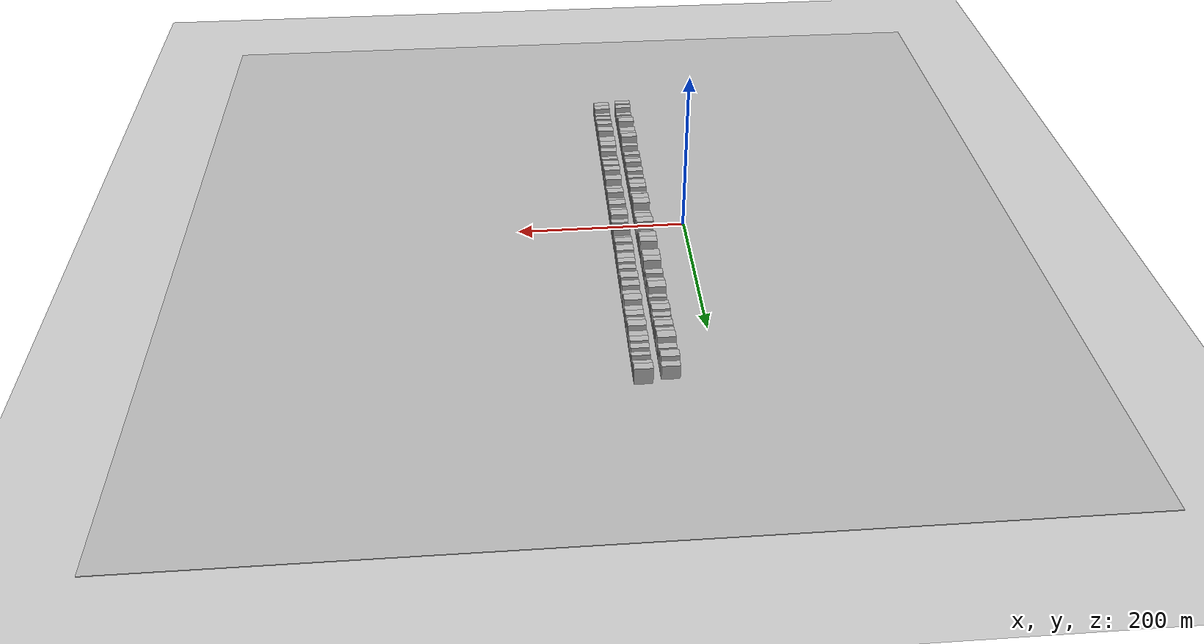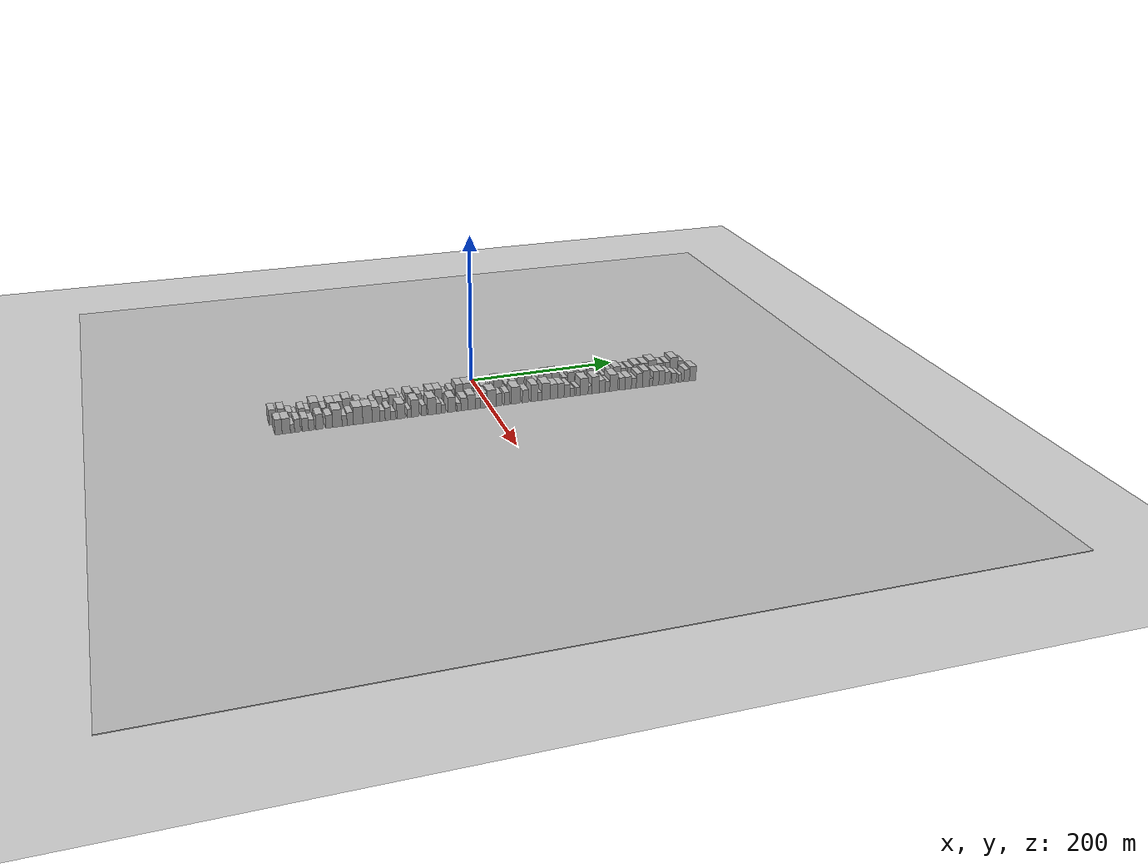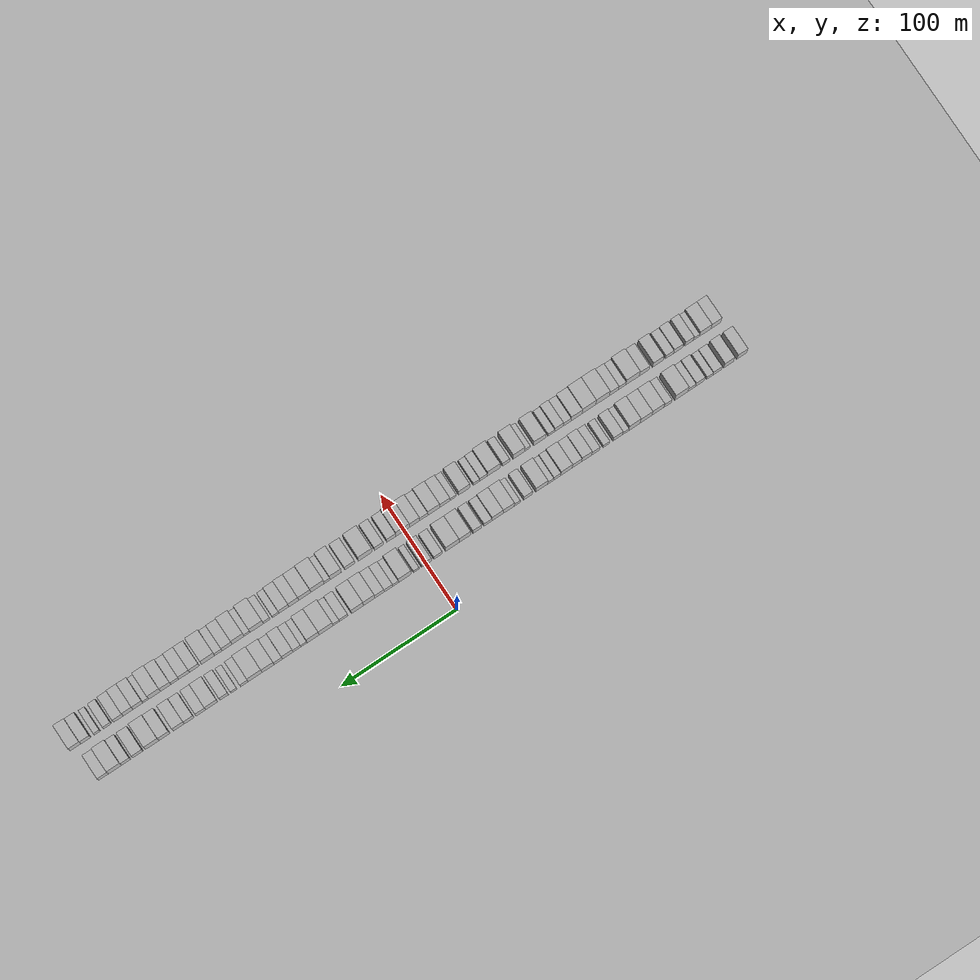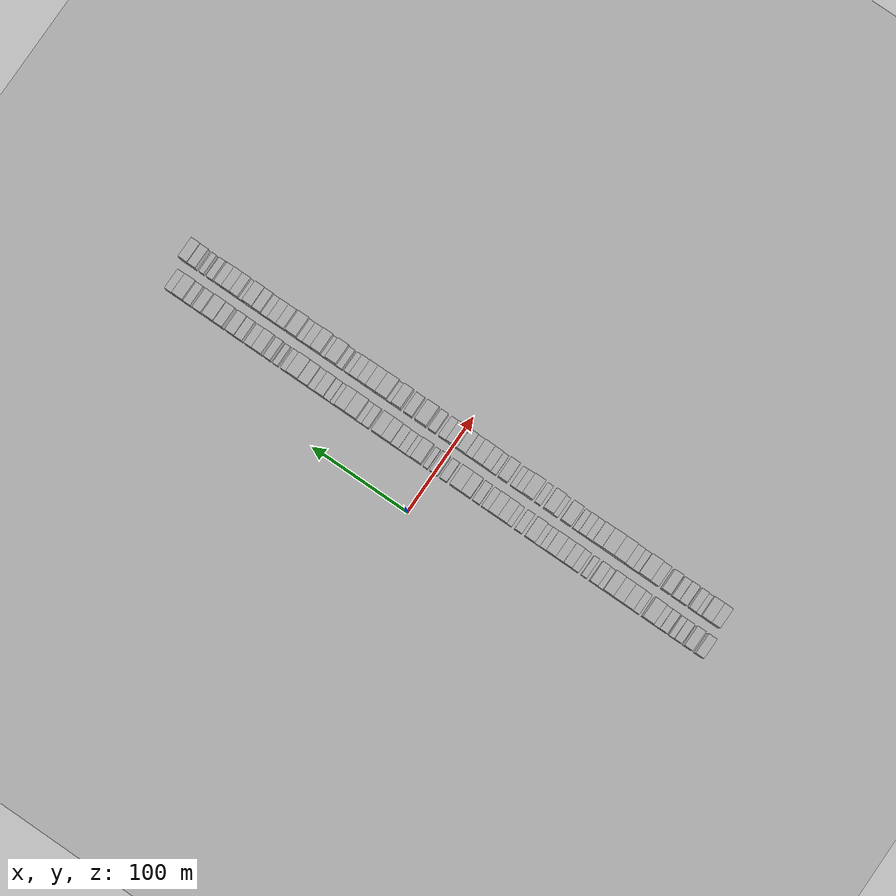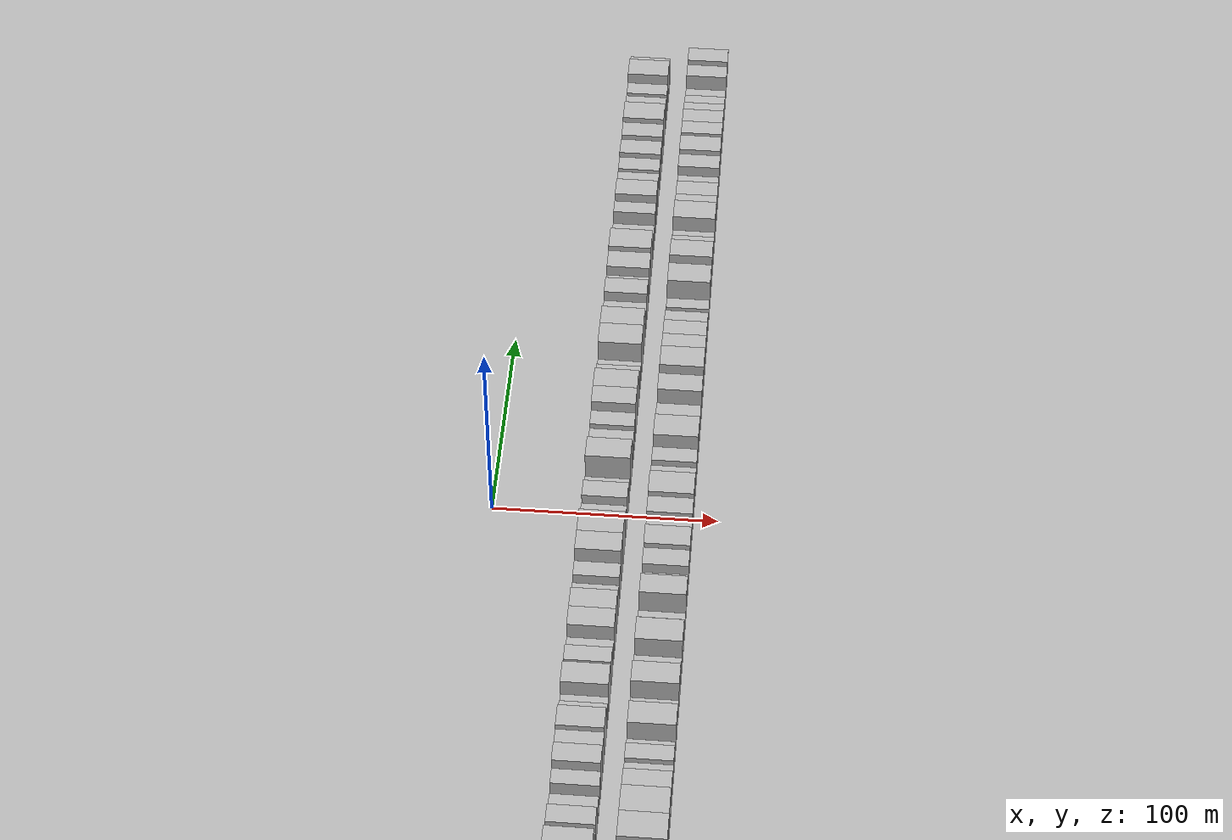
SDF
<?xml version="1.0" encoding="utf-8"?>

<sdf version="1.6">

   <world name="default">

      <gui fullscreen="0">

         <camera name="user_camera">

            <pose>-15 0 4.57585 0 0 0</pose>

            <view_controller>orbit</view_controller>

         </camera>

      </gui>

      <scene>

         <sky>

           <clouds>

             <speed>12</speed>

           </clouds>

         </sky>

         <ambient>0.4 0.4 0.4 1</ambient>

         <background>0.7 0.7 0.7 1</background>

         <shadows>1</shadows>

      </scene>

      <gravity>0 0 -9.8066</gravity>

      <magnetic_field>6e-06 2.3e-05 -4.2e-05</magnetic_field>

      <physics default="0" name="default_physics" type="ode">

         <ode>

            <solver>

               <type>quick</type>

               <iters>10</iters>

               <sor>1.0</sor>

               <use_dynamic_moi_rescaling>0</use_dynamic_moi_rescaling>

            </solver>

            <constraints>

               <cfm>0</cfm>

               <erp>0.2</erp>

               <contact_max_correcting_vel>100</contact_max_correcting_vel>

               <contact_surface_layer>0.001</contact_surface_layer>

            </constraints>

         </ode>

         <max_step_size>0.004</max_step_size>

         <real_time_factor>1</real_time_factor>

         <real_time_update_rate>250</real_time_update_rate>

      </physics>

      <light name="sun" type="directional">

         <cast_shadows>1</cast_shadows>

         <pose>0 0 10 0 0 0</pose>

         <diffuse>0.8 0.8 0.8 1</diffuse>

         <specular>0.2 0.2 0.2 1</specular>

         <attenuation>

            <range>1000</range>

            <constant>0.9</constant>

            <linear>0.01</linear>

            <quadratic>0.001</quadratic>

         </attenuation>

         <direction>-0.5 0.1 -0.9</direction>

      </light>

      <include>

         <name>ground_plane_1</name>

         <uri>model://HANNAS_ground_plane</uri>

         <pose>0 0 0  0 0 0</pose>

      </include>

      <include>

         <name>ground_plane_2</name>

         <uri>model://HANNAS_ground_plane</uri>

         <pose>100 0 0  0 0 0</pose>

      </include>

      <model name="building_1">

         <static>1</static>

         <pose frame="">50.0000 -273.7978 0 0.000000 0.000000 0.000000</pose>

         <link name="link">

            <pose frame="">0 0 10.50 0 0 0</pose>

            <collision name="collision">

               <geometry>

                  <box>

                     <size>20.0000 8.4044 21.0000</size>

                  </box>

               </geometry>

               <max_contacts>10</max_contacts>

               <surface>

                  <contact>

                     <ode/>

                  </contact>

                  <bounce/>

                  <friction>

                     <torsional>

                        <ode/>

                     </torsional>

                     <ode/>

                  </friction>

               </surface>

            </collision>

            <visual name="visual">

               <cast_shadows>0</cast_shadows>

               <geometry>

                  <box>

                     <size>20.0000 8.4044 21.0000</size>

                  </box>

               </geometry>

               <material>

                  <script>

                     <uri>model://HANNAS_wall/materials/scripts</uri>

                     <uri>model://HANNAS_wall/materials/textures</uri>

                     <name>vrc/HANNAS_wall</name>

                  </script>

               </material>

            </visual>

            <self_collide>0</self_collide>

            <enable_wind>0</enable_wind>

            <kinematic>0</kinematic>

         </link>

      </model>

      <model name="building_2">

         <static>1</static>

         <pose frame="">50.0000 -262.3265 0 0.000000 0.000000 0.000000</pose>

         <link name="link">

            <pose frame="">0 0 10.50 0 0 0</pose>

            <collision name="collision">

               <geometry>

                  <box>

                     <size>20.0000 8.5382 21.0000</size>

                  </box>

               </geometry>

               <max_contacts>10</max_contacts>

               <surface>

                  <contact>

                     <ode/>

                  </contact>

                  <bounce/>

                  <friction>

                     <torsional>

                        <ode/>

                     </torsional>

                     <ode/>

                  </friction>

               </surface>

            </collision>

            <visual name="visual">

               <cast_shadows>0</cast_shadows>

               <geometry>

                  <box>

                     <size>20.0000 8.5382 21.0000</size>

                  </box>

               </geometry>

               <material>

                  <script>

                     <uri>model://HANNAS_wall/materials/scripts</uri>

                     <uri>model://HANNAS_wall/materials/textures</uri>

                     <name>vrc/HANNAS_wall</name>

                  </script>

               </material>

            </visual>

            <self_collide>0</self_collide>

            <enable_wind>0</enable_wind>

            <kinematic>0</kinematic>

         </link>

      </model>

      <model name="building_3">

         <static>1</static>

         <pose frame="">50.0000 -252.3087 0 0.000000 0.000000 0.000000</pose>

         <link name="link">

            <pose frame="">0 0 7.50 0 0 0</pose>

            <collision name="collision">

               <geometry>

                  <box>

                     <size>20.0000 7.4974 15.0000</size>

                  </box>

               </geometry>

               <max_contacts>10</max_contacts>

               <surface>

                  <contact>

                     <ode/>

                  </contact>

                  <bounce/>

                  <friction>

                     <torsional>

                        <ode/>

                     </torsional>

                     <ode/>

                  </friction>

               </surface>

            </collision>

            <visual name="visual">

               <cast_shadows>0</cast_shadows>

               <geometry>

                  <box>

                     <size>20.0000 7.4974 15.0000</size>

                  </box>

               </geometry>

               <material>

                  <script>

                     <uri>model://HANNAS_wall/materials/scripts</uri>

                     <uri>model://HANNAS_wall/materials/textures</uri>

                     <name>vrc/HANNAS_wall</name>

                  </script>

               </material>

            </visual>

            <self_collide>0</self_collide>

            <enable_wind>0</enable_wind>

            <kinematic>0</kinematic>

         </link>

      </model>

      <model name="building_4">

         <static>1</static>

         <pose frame="">50.0000 -245.8034 0 0.000000 0.000000 0.000000</pose>

         <link name="link">

            <pose frame="">0 0 6.00 0 0 0</pose>

            <collision name="collision">

               <geometry>

                  <box>

                     <size>20.0000 5.5133 12.0000</size>

                  </box>

               </geometry>

               <max_contacts>10</max_contacts>

               <surface>

                  <contact>

                     <ode/>

                  </contact>

                  <bounce/>

                  <friction>

                     <torsional>

                        <ode/>

                     </torsional>

                     <ode/>

                  </friction>

               </surface>

            </collision>

            <visual name="visual">

               <cast_shadows>0</cast_shadows>

               <geometry>

                  <box>

                     <size>20.0000 5.5133 12.0000</size>

                  </box>

               </geometry>

               <material>

                  <script>

                     <uri>model://HANNAS_wall/materials/scripts</uri>

                     <uri>model://HANNAS_wall/materials/textures</uri>

                     <name>vrc/HANNAS_wall</name>

                  </script>

               </material>

            </visual>

            <self_collide>0</self_collide>

            <enable_wind>0</enable_wind>

            <kinematic>0</kinematic>

         </link>

      </model>

      <model name="building_5">

         <static>1</static>

         <pose frame="">50.0000 -237.1471 0 0.000000 0.000000 0.000000</pose>

         <link name="link">

            <pose frame="">0 0 9.00 0 0 0</pose>

            <collision name="collision">

               <geometry>

                  <box>

                     <size>20.0000 7.7992 18.0000</size>

                  </box>

               </geometry>

               <max_contacts>10</max_contacts>

               <surface>

                  <contact>

                     <ode/>

                  </contact>

                  <bounce/>

                  <friction>

                     <torsional>

                        <ode/>

                     </torsional>

                     <ode/>

                  </friction>

               </surface>

            </collision>

            <visual name="visual">

               <cast_shadows>0</cast_shadows>

               <geometry>

                  <box>

                     <size>20.0000 7.7992 18.0000</size>

                  </box>

               </geometry>

               <material>

                  <script>

                     <uri>model://HANNAS_wall/materials/scripts</uri>

                     <uri>model://HANNAS_wall/materials/textures</uri>

                     <name>vrc/HANNAS_wall</name>

                  </script>

               </material>

            </visual>

            <self_collide>0</self_collide>

            <enable_wind>0</enable_wind>

            <kinematic>0</kinematic>

         </link>

      </model>

      <model name="building_6">

         <static>1</static>

         <pose frame="">50.0000 -229.9238 0 0.000000 0.000000 0.000000</pose>

         <link name="link">

            <pose frame="">0 0 7.50 0 0 0</pose>

            <collision name="collision">

               <geometry>

                  <box>

                     <size>20.0000 6.6475 15.0000</size>

                  </box>

               </geometry>

               <max_contacts>10</max_contacts>

               <surface>

                  <contact>

                     <ode/>

                  </contact>

                  <bounce/>

                  <friction>

                     <torsional>

                        <ode/>

                     </torsional>

                     <ode/>

                  </friction>

               </surface>

            </collision>

            <visual name="visual">

               <cast_shadows>0</cast_shadows>

               <geometry>

                  <box>

                     <size>20.0000 6.6475 15.0000</size>

                  </box>

               </geometry>

               <material>

                  <script>

                     <uri>model://HANNAS_wall/materials/scripts</uri>

                     <uri>model://HANNAS_wall/materials/textures</uri>

                     <name>vrc/HANNAS_wall</name>

                  </script>

               </material>

            </visual>

            <self_collide>0</self_collide>

            <enable_wind>0</enable_wind>

            <kinematic>0</kinematic>

         </link>

      </model>

      <model name="building_7">

         <static>1</static>

         <pose frame="">50.0000 -220.9443 0 0.000000 0.000000 0.000000</pose>

         <link name="link">

            <pose frame="">0 0 12.00 0 0 0</pose>

            <collision name="collision">

               <geometry>

                  <box>

                     <size>20.0000 11.3114 24.0000</size>

                  </box>

               </geometry>

               <max_contacts>10</max_contacts>

               <surface>

                  <contact>

                     <ode/>

                  </contact>

                  <bounce/>

                  <friction>

                     <torsional>

                        <ode/>

                     </torsional>

                     <ode/>

                  </friction>

               </surface>

            </collision>

            <visual name="visual">

               <cast_shadows>0</cast_shadows>

               <geometry>

                  <box>

                     <size>20.0000 11.3114 24.0000</size>

                  </box>

               </geometry>

               <material>

                  <script>

                     <uri>model://HANNAS_wall/materials/scripts</uri>

                     <uri>model://HANNAS_wall/materials/textures</uri>

                     <name>vrc/HANNAS_wall</name>

                  </script>

               </material>

            </visual>

            <self_collide>0</self_collide>

            <enable_wind>0</enable_wind>

            <kinematic>0</kinematic>

         </link>

      </model>

      <model name="building_8">

         <static>1</static>

         <pose frame="">50.0000 -208.9411 0 0.000000 0.000000 0.000000</pose>

         <link name="link">

            <pose frame="">0 0 7.50 0 0 0</pose>

            <collision name="collision">

               <geometry>

                  <box>

                     <size>20.0000 6.6950 15.0000</size>

                  </box>

               </geometry>

               <max_contacts>10</max_contacts>

               <surface>

                  <contact>

                     <ode/>

                  </contact>

                  <bounce/>

                  <friction>

                     <torsional>

                        <ode/>

                     </torsional>

                     <ode/>

                  </friction>

               </surface>

            </collision>

            <visual name="visual">

               <cast_shadows>0</cast_shadows>

               <geometry>

                  <box>

                     <size>20.0000 6.6950 15.0000</size>

                  </box>

               </geometry>

               <material>

                  <script>

                     <uri>model://HANNAS_wall/materials/scripts</uri>

                     <uri>model://HANNAS_wall/materials/textures</uri>

                     <name>vrc/HANNAS_wall</name>

                  </script>

               </material>

            </visual>

            <self_collide>0</self_collide>

            <enable_wind>0</enable_wind>

            <kinematic>0</kinematic>

         </link>

      </model>

      <model name="building_9">

         <static>1</static>

         <pose frame="">50.0000 -200.4397 0 0.000000 0.000000 0.000000</pose>

         <link name="link">

            <pose frame="">0 0 10.50 0 0 0</pose>

            <collision name="collision">

               <geometry>

                  <box>

                     <size>20.0000 10.3080 21.0000</size>

                  </box>

               </geometry>

               <max_contacts>10</max_contacts>

               <surface>

                  <contact>

                     <ode/>

                  </contact>

                  <bounce/>

                  <friction>

                     <torsional>

                        <ode/>

                     </torsional>

                     <ode/>

                  </friction>

               </surface>

            </collision>

            <visual name="visual">

               <cast_shadows>0</cast_shadows>

               <geometry>

                  <box>

                     <size>20.0000 10.3080 21.0000</size>

                  </box>

               </geometry>

               <material>

                  <script>

                     <uri>model://HANNAS_wall/materials/scripts</uri>

                     <uri>model://HANNAS_wall/materials/textures</uri>

                     <name>vrc/HANNAS_wall</name>

                  </script>

               </material>

            </visual>

            <self_collide>0</self_collide>

            <enable_wind>0</enable_wind>

            <kinematic>0</kinematic>

         </link>

      </model>

      <model name="building_10">

         <static>1</static>

         <pose frame="">50.0000 -190.1663 0 0.000000 0.000000 0.000000</pose>

         <link name="link">

            <pose frame="">0 0 10.50 0 0 0</pose>

            <collision name="collision">

               <geometry>

                  <box>

                     <size>20.0000 10.2386 21.0000</size>

                  </box>

               </geometry>

               <max_contacts>10</max_contacts>

               <surface>

                  <contact>

                     <ode/>

                  </contact>

                  <bounce/>

                  <friction>

                     <torsional>

                        <ode/>

                     </torsional>

                     <ode/>

                  </friction>

               </surface>

            </collision>

            <visual name="visual">

               <cast_shadows>0</cast_shadows>

               <geometry>

                  <box>

                     <size>20.0000 10.2386 21.0000</size>

                  </box>

               </geometry>

               <material>

                  <script>

                     <uri>model://HANNAS_wall/materials/scripts</uri>

                     <uri>model://HANNAS_wall/materials/textures</uri>

                     <name>vrc/HANNAS_wall</name>

                  </script>

               </material>

            </visual>

            <self_collide>0</self_collide>

            <enable_wind>0</enable_wind>

            <kinematic>0</kinematic>

         </link>

      </model>

      <model name="building_11">

         <static>1</static>

         <pose frame="">50.0000 -180.0486 0 0.000000 0.000000 0.000000</pose>

         <link name="link">

            <pose frame="">0 0 12.00 0 0 0</pose>

            <collision name="collision">

               <geometry>

                  <box>

                     <size>20.0000 9.9968 24.0000</size>

                  </box>

               </geometry>

               <max_contacts>10</max_contacts>

               <surface>

                  <contact>

                     <ode/>

                  </contact>

                  <bounce/>

                  <friction>

                     <torsional>

                        <ode/>

                     </torsional>

                     <ode/>

                  </friction>

               </surface>

            </collision>

            <visual name="visual">

               <cast_shadows>0</cast_shadows>

               <geometry>

                  <box>

                     <size>20.0000 9.9968 24.0000</size>

                  </box>

               </geometry>

               <material>

                  <script>

                     <uri>model://HANNAS_wall/materials/scripts</uri>

                     <uri>model://HANNAS_wall/materials/textures</uri>

                     <name>vrc/HANNAS_wall</name>

                  </script>

               </material>

            </visual>

            <self_collide>0</self_collide>

            <enable_wind>0</enable_wind>

            <kinematic>0</kinematic>

         </link>

      </model>

      <model name="building_12">

         <static>1</static>

         <pose frame="">50.0000 -172.3414 0 0.000000 0.000000 0.000000</pose>

         <link name="link">

            <pose frame="">0 0 6.00 0 0 0</pose>

            <collision name="collision">

               <geometry>

                  <box>

                     <size>20.0000 5.4176 12.0000</size>

                  </box>

               </geometry>

               <max_contacts>10</max_contacts>

               <surface>

                  <contact>

                     <ode/>

                  </contact>

                  <bounce/>

                  <friction>

                     <torsional>

                        <ode/>

                     </torsional>

                     <ode/>

                  </friction>

               </surface>

            </collision>

            <visual name="visual">

               <cast_shadows>0</cast_shadows>

               <geometry>

                  <box>

                     <size>20.0000 5.4176 12.0000</size>

                  </box>

               </geometry>

               <material>

                  <script>

                     <uri>model://HANNAS_wall/materials/scripts</uri>

                     <uri>model://HANNAS_wall/materials/textures</uri>

                     <name>vrc/HANNAS_wall</name>

                  </script>

               </material>

            </visual>

            <self_collide>0</self_collide>

            <enable_wind>0</enable_wind>

            <kinematic>0</kinematic>

         </link>

      </model>

      <model name="building_13">

         <static>1</static>

         <pose frame="">50.0000 -165.5257 0 0.000000 0.000000 0.000000</pose>

         <link name="link">

            <pose frame="">0 0 9.00 0 0 0</pose>

            <collision name="collision">

               <geometry>

                  <box>

                     <size>20.0000 8.2139 18.0000</size>

                  </box>

               </geometry>

               <max_contacts>10</max_contacts>

               <surface>

                  <contact>

                     <ode/>

                  </contact>

                  <bounce/>

                  <friction>

                     <torsional>

                        <ode/>

                     </torsional>

                     <ode/>

                  </friction>

               </surface>

            </collision>

            <visual name="visual">

               <cast_shadows>0</cast_shadows>

               <geometry>

                  <box>

                     <size>20.0000 8.2139 18.0000</size>

                  </box>

               </geometry>

               <material>

                  <script>

                     <uri>model://HANNAS_wall/materials/scripts</uri>

                     <uri>model://HANNAS_wall/materials/textures</uri>

                     <name>vrc/HANNAS_wall</name>

                  </script>

               </material>

            </visual>

            <self_collide>0</self_collide>

            <enable_wind>0</enable_wind>

            <kinematic>0</kinematic>

         </link>

      </model>

      <model name="building_14">

         <static>1</static>

         <pose frame="">50.0000 -155.6016 0 0.000000 0.000000 0.000000</pose>

         <link name="link">

            <pose frame="">0 0 6.00 0 0 0</pose>

            <collision name="collision">

               <geometry>

                  <box>

                     <size>20.0000 5.6343 12.0000</size>

                  </box>

               </geometry>

               <max_contacts>10</max_contacts>

               <surface>

                  <contact>

                     <ode/>

                  </contact>

                  <bounce/>

                  <friction>

                     <torsional>

                        <ode/>

                     </torsional>

                     <ode/>

                  </friction>

               </surface>

            </collision>

            <visual name="visual">

               <cast_shadows>0</cast_shadows>

               <geometry>

                  <box>

                     <size>20.0000 5.6343 12.0000</size>

                  </box>

               </geometry>

               <material>

                  <script>

                     <uri>model://HANNAS_wall/materials/scripts</uri>

                     <uri>model://HANNAS_wall/materials/textures</uri>

                     <name>vrc/HANNAS_wall</name>

                  </script>

               </material>

            </visual>

            <self_collide>0</self_collide>

            <enable_wind>0</enable_wind>

            <kinematic>0</kinematic>

         </link>

      </model>

      <model name="building_15">

         <static>1</static>

         <pose frame="">50.0000 -146.2886 0 0.000000 0.000000 0.000000</pose>

         <link name="link">

            <pose frame="">0 0 7.50 0 0 0</pose>

            <collision name="collision">

               <geometry>

                  <box>

                     <size>20.0000 6.9917 15.0000</size>

                  </box>

               </geometry>

               <max_contacts>10</max_contacts>

               <surface>

                  <contact>

                     <ode/>

                  </contact>

                  <bounce/>

                  <friction>

                     <torsional>

                        <ode/>

                     </torsional>

                     <ode/>

                  </friction>

               </surface>

            </collision>

            <visual name="visual">

               <cast_shadows>0</cast_shadows>

               <geometry>

                  <box>

                     <size>20.0000 6.9917 15.0000</size>

                  </box>

               </geometry>

               <material>

                  <script>

                     <uri>model://HANNAS_wall/materials/scripts</uri>

                     <uri>model://HANNAS_wall/materials/textures</uri>

                     <name>vrc/HANNAS_wall</name>

                  </script>

               </material>

            </visual>

            <self_collide>0</self_collide>

            <enable_wind>0</enable_wind>

            <kinematic>0</kinematic>

         </link>

      </model>

      <model name="building_16">

         <static>1</static>

         <pose frame="">50.0000 -138.4648 0 0.000000 0.000000 0.000000</pose>

         <link name="link">

            <pose frame="">0 0 10.50 0 0 0</pose>

            <collision name="collision">

               <geometry>

                  <box>

                     <size>20.0000 8.6559 21.0000</size>

                  </box>

               </geometry>

               <max_contacts>10</max_contacts>

               <surface>

                  <contact>

                     <ode/>

                  </contact>

                  <bounce/>

                  <friction>

                     <torsional>

                        <ode/>

                     </torsional>

                     <ode/>

                  </friction>

               </surface>

            </collision>

            <visual name="visual">

               <cast_shadows>0</cast_shadows>

               <geometry>

                  <box>

                     <size>20.0000 8.6559 21.0000</size>

                  </box>

               </geometry>

               <material>

                  <script>

                     <uri>model://HANNAS_wall/materials/scripts</uri>

                     <uri>model://HANNAS_wall/materials/textures</uri>

                     <name>vrc/HANNAS_wall</name>

                  </script>

               </material>

            </visual>

            <self_collide>0</self_collide>

            <enable_wind>0</enable_wind>

            <kinematic>0</kinematic>

         </link>

      </model>

      <model name="building_17">

         <static>1</static>

         <pose frame="">50.0000 -130.0193 0 0.000000 0.000000 0.000000</pose>

         <link name="link">

            <pose frame="">0 0 9.00 0 0 0</pose>

            <collision name="collision">

               <geometry>

                  <box>

                     <size>20.0000 8.2351 18.0000</size>

                  </box>

               </geometry>

               <max_contacts>10</max_contacts>

               <surface>

                  <contact>

                     <ode/>

                  </contact>

                  <bounce/>

                  <friction>

                     <torsional>

                        <ode/>

                     </torsional>

                     <ode/>

                  </friction>

               </surface>

            </collision>

            <visual name="visual">

               <cast_shadows>0</cast_shadows>

               <geometry>

                  <box>

                     <size>20.0000 8.2351 18.0000</size>

                  </box>

               </geometry>

               <material>

                  <script>

                     <uri>model://HANNAS_wall/materials/scripts</uri>

                     <uri>model://HANNAS_wall/materials/textures</uri>

                     <name>vrc/HANNAS_wall</name>

                  </script>

               </material>

            </visual>

            <self_collide>0</self_collide>

            <enable_wind>0</enable_wind>

            <kinematic>0</kinematic>

         </link>

      </model>

      <model name="building_18">

         <static>1</static>

         <pose frame="">50.0000 -120.9376 0 0.000000 0.000000 0.000000</pose>

         <link name="link">

            <pose frame="">0 0 10.50 0 0 0</pose>

            <collision name="collision">

               <geometry>

                  <box>

                     <size>20.0000 9.9283 21.0000</size>

                  </box>

               </geometry>

               <max_contacts>10</max_contacts>

               <surface>

                  <contact>

                     <ode/>

                  </contact>

                  <bounce/>

                  <friction>

                     <torsional>

                        <ode/>

                     </torsional>

                     <ode/>

                  </friction>

               </surface>

            </collision>

            <visual name="visual">

               <cast_shadows>0</cast_shadows>

               <geometry>

                  <box>

                     <size>20.0000 9.9283 21.0000</size>

                  </box>

               </geometry>

               <material>

                  <script>

                     <uri>model://HANNAS_wall/materials/scripts</uri>

                     <uri>model://HANNAS_wall/materials/textures</uri>

                     <name>vrc/HANNAS_wall</name>

                  </script>

               </material>

            </visual>

            <self_collide>0</self_collide>

            <enable_wind>0</enable_wind>

            <kinematic>0</kinematic>

         </link>

      </model>

      <model name="building_19">

         <static>1</static>

         <pose frame="">50.0000 -112.9268 0 0.000000 0.000000 0.000000</pose>

         <link name="link">

            <pose frame="">0 0 7.50 0 0 0</pose>

            <collision name="collision">

               <geometry>

                  <box>

                     <size>20.0000 6.0931 15.0000</size>

                  </box>

               </geometry>

               <max_contacts>10</max_contacts>

               <surface>

                  <contact>

                     <ode/>

                  </contact>

                  <bounce/>

                  <friction>

                     <torsional>

                        <ode/>

                     </torsional>

                     <ode/>

                  </friction>

               </surface>

            </collision>

            <visual name="visual">

               <cast_shadows>0</cast_shadows>

               <geometry>

                  <box>

                     <size>20.0000 6.0931 15.0000</size>

                  </box>

               </geometry>

               <material>

                  <script>

                     <uri>model://HANNAS_wall/materials/scripts</uri>

                     <uri>model://HANNAS_wall/materials/textures</uri>

                     <name>vrc/HANNAS_wall</name>

                  </script>

               </material>

            </visual>

            <self_collide>0</self_collide>

            <enable_wind>0</enable_wind>

            <kinematic>0</kinematic>

         </link>

      </model>

      <model name="building_20">

         <static>1</static>

         <pose frame="">50.0000 -107.2331 0 0.000000 0.000000 0.000000</pose>

         <link name="link">

            <pose frame="">0 0 6.00 0 0 0</pose>

            <collision name="collision">

               <geometry>

                  <box>

                     <size>20.0000 5.2942 12.0000</size>

                  </box>

               </geometry>

               <max_contacts>10</max_contacts>

               <surface>

                  <contact>

                     <ode/>

                  </contact>

                  <bounce/>

                  <friction>

                     <torsional>

                        <ode/>

                     </torsional>

                     <ode/>

                  </friction>

               </surface>

            </collision>

            <visual name="visual">

               <cast_shadows>0</cast_shadows>

               <geometry>

                  <box>

                     <size>20.0000 5.2942 12.0000</size>

                  </box>

               </geometry>

               <material>

                  <script>

                     <uri>model://HANNAS_wall/materials/scripts</uri>

                     <uri>model://HANNAS_wall/materials/textures</uri>

                     <name>vrc/HANNAS_wall</name>

                  </script>

               </material>

            </visual>

            <self_collide>0</self_collide>

            <enable_wind>0</enable_wind>

            <kinematic>0</kinematic>

         </link>

      </model>

      <model name="building_21">

         <static>1</static>

         <pose frame="">50.0000 -99.4346 0 0.000000 0.000000 0.000000</pose>

         <link name="link">

            <pose frame="">0 0 10.50 0 0 0</pose>

            <collision name="collision">

               <geometry>

                  <box>

                     <size>20.0000 10.3028 21.0000</size>

                  </box>

               </geometry>

               <max_contacts>10</max_contacts>

               <surface>

                  <contact>

                     <ode/>

                  </contact>

                  <bounce/>

                  <friction>

                     <torsional>

                        <ode/>

                     </torsional>

                     <ode/>

                  </friction>

               </surface>

            </collision>

            <visual name="visual">

               <cast_shadows>0</cast_shadows>

               <geometry>

                  <box>

                     <size>20.0000 10.3028 21.0000</size>

                  </box>

               </geometry>

               <material>

                  <script>

                     <uri>model://HANNAS_wall/materials/scripts</uri>

                     <uri>model://HANNAS_wall/materials/textures</uri>

                     <name>vrc/HANNAS_wall</name>

                  </script>

               </material>

            </visual>

            <self_collide>0</self_collide>

            <enable_wind>0</enable_wind>

            <kinematic>0</kinematic>

         </link>

      </model>

      <model name="building_22">

         <static>1</static>

         <pose frame="">50.0000 -87.5052 0 0.000000 0.000000 0.000000</pose>

         <link name="link">

            <pose frame="">0 0 9.00 0 0 0</pose>

            <collision name="collision">

               <geometry>

                  <box>

                     <size>20.0000 7.5561 18.0000</size>

                  </box>

               </geometry>

               <max_contacts>10</max_contacts>

               <surface>

                  <contact>

                     <ode/>

                  </contact>

                  <bounce/>

                  <friction>

                     <torsional>

                        <ode/>

                     </torsional>

                     <ode/>

                  </friction>

               </surface>

            </collision>

            <visual name="visual">

               <cast_shadows>0</cast_shadows>

               <geometry>

                  <box>

                     <size>20.0000 7.5561 18.0000</size>

                  </box>

               </geometry>

               <material>

                  <script>

                     <uri>model://HANNAS_wall/materials/scripts</uri>

                     <uri>model://HANNAS_wall/materials/textures</uri>

                     <name>vrc/HANNAS_wall</name>

                  </script>

               </material>

            </visual>

            <self_collide>0</self_collide>

            <enable_wind>0</enable_wind>

            <kinematic>0</kinematic>

         </link>

      </model>

      <model name="building_23">

         <static>1</static>

         <pose frame="">50.0000 -78.1779 0 0.000000 0.000000 0.000000</pose>

         <link name="link">

            <pose frame="">0 0 6.00 0 0 0</pose>

            <collision name="collision">

               <geometry>

                  <box>

                     <size>20.0000 5.0985 12.0000</size>

                  </box>

               </geometry>

               <max_contacts>10</max_contacts>

               <surface>

                  <contact>

                     <ode/>

                  </contact>

                  <bounce/>

                  <friction>

                     <torsional>

                        <ode/>

                     </torsional>

                     <ode/>

                  </friction>

               </surface>

            </collision>

            <visual name="visual">

               <cast_shadows>0</cast_shadows>

               <geometry>

                  <box>

                     <size>20.0000 5.0985 12.0000</size>

                  </box>

               </geometry>

               <material>

                  <script>

                     <uri>model://HANNAS_wall/materials/scripts</uri>

                     <uri>model://HANNAS_wall/materials/textures</uri>

                     <name>vrc/HANNAS_wall</name>

                  </script>

               </material>

            </visual>

            <self_collide>0</self_collide>

            <enable_wind>0</enable_wind>

            <kinematic>0</kinematic>

         </link>

      </model>

      <model name="building_24">

         <static>1</static>

         <pose frame="">50.0000 -70.7922 0 0.000000 0.000000 0.000000</pose>

         <link name="link">

            <pose frame="">0 0 10.50 0 0 0</pose>

            <collision name="collision">

               <geometry>

                  <box>

                     <size>20.0000 9.6729 21.0000</size>

                  </box>

               </geometry>

               <max_contacts>10</max_contacts>

               <surface>

                  <contact>

                     <ode/>

                  </contact>

                  <bounce/>

                  <friction>

                     <torsional>

                        <ode/>

                     </torsional>

                     <ode/>

                  </friction>

               </surface>

            </collision>

            <visual name="visual">

               <cast_shadows>0</cast_shadows>

               <geometry>

                  <box>

                     <size>20.0000 9.6729 21.0000</size>

                  </box>

               </geometry>

               <material>

                  <script>

                     <uri>model://HANNAS_wall/materials/scripts</uri>

                     <uri>model://HANNAS_wall/materials/textures</uri>

                     <name>vrc/HANNAS_wall</name>

                  </script>

               </material>

            </visual>

            <self_collide>0</self_collide>

            <enable_wind>0</enable_wind>

            <kinematic>0</kinematic>

         </link>

      </model>

      <model name="building_25">

         <static>1</static>

         <pose frame="">50.0000 -61.1262 0 0.000000 0.000000 0.000000</pose>

         <link name="link">

            <pose frame="">0 0 10.50 0 0 0</pose>

            <collision name="collision">

               <geometry>

                  <box>

                     <size>20.0000 9.6592 21.0000</size>

                  </box>

               </geometry>

               <max_contacts>10</max_contacts>

               <surface>

                  <contact>

                     <ode/>

                  </contact>

                  <bounce/>

                  <friction>

                     <torsional>

                        <ode/>

                     </torsional>

                     <ode/>

                  </friction>

               </surface>

            </collision>

            <visual name="visual">

               <cast_shadows>0</cast_shadows>

               <geometry>

                  <box>

                     <size>20.0000 9.6592 21.0000</size>

                  </box>

               </geometry>

               <material>

                  <script>

                     <uri>model://HANNAS_wall/materials/scripts</uri>

                     <uri>model://HANNAS_wall/materials/textures</uri>

                     <name>vrc/HANNAS_wall</name>

                  </script>

               </material>

            </visual>

            <self_collide>0</self_collide>

            <enable_wind>0</enable_wind>

            <kinematic>0</kinematic>

         </link>

      </model>

      <model name="building_26">

         <static>1</static>

         <pose frame="">50.0000 -52.8360 0 0.000000 0.000000 0.000000</pose>

         <link name="link">

            <pose frame="">0 0 7.50 0 0 0</pose>

            <collision name="collision">

               <geometry>

                  <box>

                     <size>20.0000 6.9211 15.0000</size>

                  </box>

               </geometry>

               <max_contacts>10</max_contacts>

               <surface>

                  <contact>

                     <ode/>

                  </contact>

                  <bounce/>

                  <friction>

                     <torsional>

                        <ode/>

                     </torsional>

                     <ode/>

                  </friction>

               </surface>

            </collision>

            <visual name="visual">

               <cast_shadows>0</cast_shadows>

               <geometry>

                  <box>

                     <size>20.0000 6.9211 15.0000</size>

                  </box>

               </geometry>

               <material>

                  <script>

                     <uri>model://HANNAS_wall/materials/scripts</uri>

                     <uri>model://HANNAS_wall/materials/textures</uri>

                     <name>vrc/HANNAS_wall</name>

                  </script>

               </material>

            </visual>

            <self_collide>0</self_collide>

            <enable_wind>0</enable_wind>

            <kinematic>0</kinematic>

         </link>

      </model>

      <model name="building_27">

         <static>1</static>

         <pose frame="">50.0000 -43.6139 0 0.000000 0.000000 0.000000</pose>

         <link name="link">

            <pose frame="">0 0 9.00 0 0 0</pose>

            <collision name="collision">

               <geometry>

                  <box>

                     <size>20.0000 7.5232 18.0000</size>

                  </box>

               </geometry>

               <max_contacts>10</max_contacts>

               <surface>

                  <contact>

                     <ode/>

                  </contact>

                  <bounce/>

                  <friction>

                     <torsional>

                        <ode/>

                     </torsional>

                     <ode/>

                  </friction>

               </surface>

            </collision>

            <visual name="visual">

               <cast_shadows>0</cast_shadows>

               <geometry>

                  <box>

                     <size>20.0000 7.5232 18.0000</size>

                  </box>

               </geometry>

               <material>

                  <script>

                     <uri>model://HANNAS_wall/materials/scripts</uri>

                     <uri>model://HANNAS_wall/materials/textures</uri>

                     <name>vrc/HANNAS_wall</name>

                  </script>

               </material>

            </visual>

            <self_collide>0</self_collide>

            <enable_wind>0</enable_wind>

            <kinematic>0</kinematic>

         </link>

      </model>

      <model name="building_28">

         <static>1</static>

         <pose frame="">50.0000 -32.9053 0 0.000000 0.000000 0.000000</pose>

         <link name="link">

            <pose frame="">0 0 12.00 0 0 0</pose>

            <collision name="collision">

               <geometry>

                  <box>

                     <size>20.0000 9.8939 24.0000</size>

                  </box>

               </geometry>

               <max_contacts>10</max_contacts>

               <surface>

                  <contact>

                     <ode/>

                  </contact>

                  <bounce/>

                  <friction>

                     <torsional>

                        <ode/>

                     </torsional>

                     <ode/>

                  </friction>

               </surface>

            </collision>

            <visual name="visual">

               <cast_shadows>0</cast_shadows>

               <geometry>

                  <box>

                     <size>20.0000 9.8939 24.0000</size>

                  </box>

               </geometry>

               <material>

                  <script>

                     <uri>model://HANNAS_wall/materials/scripts</uri>

                     <uri>model://HANNAS_wall/materials/textures</uri>

                     <name>vrc/HANNAS_wall</name>

                  </script>

               </material>

            </visual>

            <self_collide>0</self_collide>

            <enable_wind>0</enable_wind>

            <kinematic>0</kinematic>

         </link>

      </model>

      <model name="building_29">

         <static>1</static>

         <pose frame="">50.0000 -22.1314 0 0.000000 0.000000 0.000000</pose>

         <link name="link">

            <pose frame="">0 0 12.00 0 0 0</pose>

            <collision name="collision">

               <geometry>

                  <box>

                     <size>20.0000 11.6541 24.0000</size>

                  </box>

               </geometry>

               <max_contacts>10</max_contacts>

               <surface>

                  <contact>

                     <ode/>

                  </contact>

                  <bounce/>

                  <friction>

                     <torsional>

                        <ode/>

                     </torsional>

                     <ode/>

                  </friction>

               </surface>

            </collision>

            <visual name="visual">

               <cast_shadows>0</cast_shadows>

               <geometry>

                  <box>

                     <size>20.0000 11.6541 24.0000</size>

                  </box>

               </geometry>

               <material>

                  <script>

                     <uri>model://HANNAS_wall/materials/scripts</uri>

                     <uri>model://HANNAS_wall/materials/textures</uri>

                     <name>vrc/HANNAS_wall</name>

                  </script>

               </material>

            </visual>

            <self_collide>0</self_collide>

            <enable_wind>0</enable_wind>

            <kinematic>0</kinematic>

         </link>

      </model>

      <model name="building_30">

         <static>1</static>

         <pose frame="">50.0000 -9.6206 0 0.000000 0.000000 0.000000</pose>

         <link name="link">

            <pose frame="">0 0 7.50 0 0 0</pose>

            <collision name="collision">

               <geometry>

                  <box>

                     <size>20.0000 7.3675 15.0000</size>

                  </box>

               </geometry>

               <max_contacts>10</max_contacts>

               <surface>

                  <contact>

                     <ode/>

                  </contact>

                  <bounce/>

                  <friction>

                     <torsional>

                        <ode/>

                     </torsional>

                     <ode/>

                  </friction>

               </surface>

            </collision>

            <visual name="visual">

               <cast_shadows>0</cast_shadows>

               <geometry>

                  <box>

                     <size>20.0000 7.3675 15.0000</size>

                  </box>

               </geometry>

               <material>

                  <script>

                     <uri>model://HANNAS_wall/materials/scripts</uri>

                     <uri>model://HANNAS_wall/materials/textures</uri>

                     <name>vrc/HANNAS_wall</name>

                  </script>

               </material>

            </visual>

            <self_collide>0</self_collide>

            <enable_wind>0</enable_wind>

            <kinematic>0</kinematic>

         </link>

      </model>

      <model name="building_31">

         <static>1</static>

         <pose frame="">50.0000 0.3576 0 0.000000 0.000000 0.000000</pose>

         <link name="link">

            <pose frame="">0 0 9.00 0 0 0</pose>

            <collision name="collision">

               <geometry>

                  <box>

                     <size>20.0000 8.5888 18.0000</size>

                  </box>

               </geometry>

               <max_contacts>10</max_contacts>

               <surface>

                  <contact>

                     <ode/>

                  </contact>

                  <bounce/>

                  <friction>

                     <torsional>

                        <ode/>

                     </torsional>

                     <ode/>

                  </friction>

               </surface>

            </collision>

            <visual name="visual">

               <cast_shadows>0</cast_shadows>

               <geometry>

                  <box>

                     <size>20.0000 8.5888 18.0000</size>

                  </box>

               </geometry>

               <material>

                  <script>

                     <uri>model://HANNAS_wall/materials/scripts</uri>

                     <uri>model://HANNAS_wall/materials/textures</uri>

                     <name>vrc/HANNAS_wall</name>

                  </script>

               </material>

            </visual>

            <self_collide>0</self_collide>

            <enable_wind>0</enable_wind>

            <kinematic>0</kinematic>

         </link>

      </model>

      <model name="building_32">

         <static>1</static>

         <pose frame="">50.0000 9.0970 0 0.000000 0.000000 0.000000</pose>

         <link name="link">

            <pose frame="">0 0 6.00 0 0 0</pose>

            <collision name="collision">

               <geometry>

                  <box>

                     <size>20.0000 4.8899 12.0000</size>

                  </box>

               </geometry>

               <max_contacts>10</max_contacts>

               <surface>

                  <contact>

                     <ode/>

                  </contact>

                  <bounce/>

                  <friction>

                     <torsional>

                        <ode/>

                     </torsional>

                     <ode/>

                  </friction>

               </surface>

            </collision>

            <visual name="visual">

               <cast_shadows>0</cast_shadows>

               <geometry>

                  <box>

                     <size>20.0000 4.8899 12.0000</size>

                  </box>

               </geometry>

               <material>

                  <script>

                     <uri>model://HANNAS_wall/materials/scripts</uri>

                     <uri>model://HANNAS_wall/materials/textures</uri>

                     <name>vrc/HANNAS_wall</name>

                  </script>

               </material>

            </visual>

            <self_collide>0</self_collide>

            <enable_wind>0</enable_wind>

            <kinematic>0</kinematic>

         </link>

      </model>

      <model name="building_33">

         <static>1</static>

         <pose frame="">50.0000 18.9755 0 0.000000 0.000000 0.000000</pose>

         <link name="link">

            <pose frame="">0 0 12.00 0 0 0</pose>

            <collision name="collision">

               <geometry>

                  <box>

                     <size>20.0000 10.8672 24.0000</size>

                  </box>

               </geometry>

               <max_contacts>10</max_contacts>

               <surface>

                  <contact>

                     <ode/>

                  </contact>

                  <bounce/>

                  <friction>

                     <torsional>

                        <ode/>

                     </torsional>

                     <ode/>

                  </friction>

               </surface>

            </collision>

            <visual name="visual">

               <cast_shadows>0</cast_shadows>

               <geometry>

                  <box>

                     <size>20.0000 10.8672 24.0000</size>

                  </box>

               </geometry>

               <material>

                  <script>

                     <uri>model://HANNAS_wall/materials/scripts</uri>

                     <uri>model://HANNAS_wall/materials/textures</uri>

                     <name>vrc/HANNAS_wall</name>

                  </script>

               </material>

            </visual>

            <self_collide>0</self_collide>

            <enable_wind>0</enable_wind>

            <kinematic>0</kinematic>

         </link>

      </model>

      <model name="building_34">

         <static>1</static>

         <pose frame="">50.0000 26.9637 0 0.000000 0.000000 0.000000</pose>

         <link name="link">

            <pose frame="">0 0 6.00 0 0 0</pose>

            <collision name="collision">

               <geometry>

                  <box>

                     <size>20.0000 5.1092 12.0000</size>

                  </box>

               </geometry>

               <max_contacts>10</max_contacts>

               <surface>

                  <contact>

                     <ode/>

                  </contact>

                  <bounce/>

                  <friction>

                     <torsional>

                        <ode/>

                     </torsional>

                     <ode/>

                  </friction>

               </surface>

            </collision>

            <visual name="visual">

               <cast_shadows>0</cast_shadows>

               <geometry>

                  <box>

                     <size>20.0000 5.1092 12.0000</size>

                  </box>

               </geometry>

               <material>

                  <script>

                     <uri>model://HANNAS_wall/materials/scripts</uri>

                     <uri>model://HANNAS_wall/materials/textures</uri>

                     <name>vrc/HANNAS_wall</name>

                  </script>

               </material>

            </visual>

            <self_collide>0</self_collide>

            <enable_wind>0</enable_wind>

            <kinematic>0</kinematic>

         </link>

      </model>

      <model name="building_35">

         <static>1</static>

         <pose frame="">50.0000 33.2226 0 0.000000 0.000000 0.000000</pose>

         <link name="link">

            <pose frame="">0 0 7.50 0 0 0</pose>

            <collision name="collision">

               <geometry>

                  <box>

                     <size>20.0000 7.4086 15.0000</size>

                  </box>

               </geometry>

               <max_contacts>10</max_contacts>

               <surface>

                  <contact>

                     <ode/>

                  </contact>

                  <bounce/>

                  <friction>

                     <torsional>

                        <ode/>

                     </torsional>

                     <ode/>

                  </friction>

               </surface>

            </collision>

            <visual name="visual">

               <cast_shadows>0</cast_shadows>

               <geometry>

                  <box>

                     <size>20.0000 7.4086 15.0000</size>

                  </box>

               </geometry>

               <material>

                  <script>

                     <uri>model://HANNAS_wall/materials/scripts</uri>

                     <uri>model://HANNAS_wall/materials/textures</uri>

                     <name>vrc/HANNAS_wall</name>

                  </script>

               </material>

            </visual>

            <self_collide>0</self_collide>

            <enable_wind>0</enable_wind>

            <kinematic>0</kinematic>

         </link>

      </model>

      <model name="building_36">

         <static>1</static>

         <pose frame="">50.0000 40.9355 0 0.000000 0.000000 0.000000</pose>

         <link name="link">

            <pose frame="">0 0 9.00 0 0 0</pose>

            <collision name="collision">

               <geometry>

                  <box>

                     <size>20.0000 8.0170 18.0000</size>

                  </box>

               </geometry>

               <max_contacts>10</max_contacts>

               <surface>

                  <contact>

                     <ode/>

                  </contact>

                  <bounce/>

                  <friction>

                     <torsional>

                        <ode/>

                     </torsional>

                     <ode/>

                  </friction>

               </surface>

            </collision>

            <visual name="visual">

               <cast_shadows>0</cast_shadows>

               <geometry>

                  <box>

                     <size>20.0000 8.0170 18.0000</size>

                  </box>

               </geometry>

               <material>

                  <script>

                     <uri>model://HANNAS_wall/materials/scripts</uri>

                     <uri>model://HANNAS_wall/materials/textures</uri>

                     <name>vrc/HANNAS_wall</name>

                  </script>

               </material>

            </visual>

            <self_collide>0</self_collide>

            <enable_wind>0</enable_wind>

            <kinematic>0</kinematic>

         </link>

      </model>

      <model name="building_37">

         <static>1</static>

         <pose frame="">50.0000 49.7665 0 0.000000 0.000000 0.000000</pose>

         <link name="link">

            <pose frame="">0 0 12.00 0 0 0</pose>

            <collision name="collision">

               <geometry>

                  <box>

                     <size>20.0000 9.6450 24.0000</size>

                  </box>

               </geometry>

               <max_contacts>10</max_contacts>

               <surface>

                  <contact>

                     <ode/>

                  </contact>

                  <bounce/>

                  <friction>

                     <torsional>

                        <ode/>

                     </torsional>

                     <ode/>

                  </friction>

               </surface>

            </collision>

            <visual name="visual">

               <cast_shadows>0</cast_shadows>

               <geometry>

                  <box>

                     <size>20.0000 9.6450 24.0000</size>

                  </box>

               </geometry>

               <material>

                  <script>

                     <uri>model://HANNAS_wall/materials/scripts</uri>

                     <uri>model://HANNAS_wall/materials/textures</uri>

                     <name>vrc/HANNAS_wall</name>

                  </script>

               </material>

            </visual>

            <self_collide>0</self_collide>

            <enable_wind>0</enable_wind>

            <kinematic>0</kinematic>

         </link>

      </model>

      <model name="building_38">

         <static>1</static>

         <pose frame="">50.0000 59.8280 0 0.000000 0.000000 0.000000</pose>

         <link name="link">

            <pose frame="">0 0 12.00 0 0 0</pose>

            <collision name="collision">

               <geometry>

                  <box>

                     <size>20.0000 10.4779 24.0000</size>

                  </box>

               </geometry>

               <max_contacts>10</max_contacts>

               <surface>

                  <contact>

                     <ode/>

                  </contact>

                  <bounce/>

                  <friction>

                     <torsional>

                        <ode/>

                     </torsional>

                     <ode/>

                  </friction>

               </surface>

            </collision>

            <visual name="visual">

               <cast_shadows>0</cast_shadows>

               <geometry>

                  <box>

                     <size>20.0000 10.4779 24.0000</size>

                  </box>

               </geometry>

               <material>

                  <script>

                     <uri>model://HANNAS_wall/materials/scripts</uri>

                     <uri>model://HANNAS_wall/materials/textures</uri>

                     <name>vrc/HANNAS_wall</name>

                  </script>

               </material>

            </visual>

            <self_collide>0</self_collide>

            <enable_wind>0</enable_wind>

            <kinematic>0</kinematic>

         </link>

      </model>

      <model name="building_39">

         <static>1</static>

         <pose frame="">50.0000 71.7686 0 0.000000 0.000000 0.000000</pose>

         <link name="link">

            <pose frame="">0 0 7.50 0 0 0</pose>

            <collision name="collision">

               <geometry>

                  <box>

                     <size>20.0000 7.4033 15.0000</size>

                  </box>

               </geometry>

               <max_contacts>10</max_contacts>

               <surface>

                  <contact>

                     <ode/>

                  </contact>

                  <bounce/>

                  <friction>

                     <torsional>

                        <ode/>

                     </torsional>

                     <ode/>

                  </friction>

               </surface>

            </collision>

            <visual name="visual">

               <cast_shadows>0</cast_shadows>

               <geometry>

                  <box>

                     <size>20.0000 7.4033 15.0000</size>

                  </box>

               </geometry>

               <material>

                  <script>

                     <uri>model://HANNAS_wall/materials/scripts</uri>

                     <uri>model://HANNAS_wall/materials/textures</uri>

                     <name>vrc/HANNAS_wall</name>

                  </script>

               </material>

            </visual>

            <self_collide>0</self_collide>

            <enable_wind>0</enable_wind>

            <kinematic>0</kinematic>

         </link>

      </model>

      <model name="building_40">

         <static>1</static>

         <pose frame="">50.0000 78.2085 0 0.000000 0.000000 0.000000</pose>

         <link name="link">

            <pose frame="">0 0 6.00 0 0 0</pose>

            <collision name="collision">

               <geometry>

                  <box>

                     <size>20.0000 5.4766 12.0000</size>

                  </box>

               </geometry>

               <max_contacts>10</max_contacts>

               <surface>

                  <contact>

                     <ode/>

                  </contact>

                  <bounce/>

                  <friction>

                     <torsional>

                        <ode/>

                     </torsional>

                     <ode/>

                  </friction>

               </surface>

            </collision>

            <visual name="visual">

               <cast_shadows>0</cast_shadows>

               <geometry>

                  <box>

                     <size>20.0000 5.4766 12.0000</size>

                  </box>

               </geometry>

               <material>

                  <script>

                     <uri>model://HANNAS_wall/materials/scripts</uri>

                     <uri>model://HANNAS_wall/materials/textures</uri>

                     <name>vrc/HANNAS_wall</name>

                  </script>

               </material>

            </visual>

            <self_collide>0</self_collide>

            <enable_wind>0</enable_wind>

            <kinematic>0</kinematic>

         </link>

      </model>

      <model name="building_41">

         <static>1</static>

         <pose frame="">50.0000 86.9091 0 0.000000 0.000000 0.000000</pose>

         <link name="link">

            <pose frame="">0 0 12.00 0 0 0</pose>

            <collision name="collision">

               <geometry>

                  <box>

                     <size>20.0000 11.9245 24.0000</size>

                  </box>

               </geometry>

               <max_contacts>10</max_contacts>

               <surface>

                  <contact>

                     <ode/>

                  </contact>

                  <bounce/>

                  <friction>

                     <torsional>

                        <ode/>

                     </torsional>

                     <ode/>

                  </friction>

               </surface>

            </collision>

            <visual name="visual">

               <cast_shadows>0</cast_shadows>

               <geometry>

                  <box>

                     <size>20.0000 11.9245 24.0000</size>

                  </box>

               </geometry>

               <material>

                  <script>

                     <uri>model://HANNAS_wall/materials/scripts</uri>

                     <uri>model://HANNAS_wall/materials/textures</uri>

                     <name>vrc/HANNAS_wall</name>

                  </script>

               </material>

            </visual>

            <self_collide>0</self_collide>

            <enable_wind>0</enable_wind>

            <kinematic>0</kinematic>

         </link>

      </model>

      <model name="building_42">

         <static>1</static>

         <pose frame="">50.0000 98.0518 0 0.000000 0.000000 0.000000</pose>

         <link name="link">

            <pose frame="">0 0 12.00 0 0 0</pose>

            <collision name="collision">

               <geometry>

                  <box>

                     <size>20.0000 10.3611 24.0000</size>

                  </box>

               </geometry>

               <max_contacts>10</max_contacts>

               <surface>

                  <contact>

                     <ode/>

                  </contact>

                  <bounce/>

                  <friction>

                     <torsional>

                        <ode/>

                     </torsional>

                     <ode/>

                  </friction>

               </surface>

            </collision>

            <visual name="visual">

               <cast_shadows>0</cast_shadows>

               <geometry>

                  <box>

                     <size>20.0000 10.3611 24.0000</size>

                  </box>

               </geometry>

               <material>

                  <script>

                     <uri>model://HANNAS_wall/materials/scripts</uri>

                     <uri>model://HANNAS_wall/materials/textures</uri>

                     <name>vrc/HANNAS_wall</name>

                  </script>

               </material>

            </visual>

            <self_collide>0</self_collide>

            <enable_wind>0</enable_wind>

            <kinematic>0</kinematic>

         </link>

      </model>

      <model name="building_43">

         <static>1</static>

         <pose frame="">50.0000 105.8520 0 0.000000 0.000000 0.000000</pose>

         <link name="link">

            <pose frame="">0 0 6.00 0 0 0</pose>

            <collision name="collision">

               <geometry>

                  <box>

                     <size>20.0000 5.2392 12.0000</size>

                  </box>

               </geometry>

               <max_contacts>10</max_contacts>

               <surface>

                  <contact>

                     <ode/>

                  </contact>

                  <bounce/>

                  <friction>

                     <torsional>

                        <ode/>

                     </torsional>

                     <ode/>

                  </friction>

               </surface>

            </collision>

            <visual name="visual">

               <cast_shadows>0</cast_shadows>

               <geometry>

                  <box>

                     <size>20.0000 5.2392 12.0000</size>

                  </box>

               </geometry>

               <material>

                  <script>

                     <uri>model://HANNAS_wall/materials/scripts</uri>

                     <uri>model://HANNAS_wall/materials/textures</uri>

                     <name>vrc/HANNAS_wall</name>

                  </script>

               </material>

            </visual>

            <self_collide>0</self_collide>

            <enable_wind>0</enable_wind>

            <kinematic>0</kinematic>

         </link>

      </model>

      <model name="building_44">

         <static>1</static>

         <pose frame="">50.0000 111.8067 0 0.000000 0.000000 0.000000</pose>

         <link name="link">

            <pose frame="">0 0 7.50 0 0 0</pose>

            <collision name="collision">

               <geometry>

                  <box>

                     <size>20.0000 6.6703 15.0000</size>

                  </box>

               </geometry>

               <max_contacts>10</max_contacts>

               <surface>

                  <contact>

                     <ode/>

                  </contact>

                  <bounce/>

                  <friction>

                     <torsional>

                        <ode/>

                     </torsional>

                     <ode/>

                  </friction>

               </surface>

            </collision>

            <visual name="visual">

               <cast_shadows>0</cast_shadows>

               <geometry>

                  <box>

                     <size>20.0000 6.6703 15.0000</size>

                  </box>

               </geometry>

               <material>

                  <script>

                     <uri>model://HANNAS_wall/materials/scripts</uri>

                     <uri>model://HANNAS_wall/materials/textures</uri>

                     <name>vrc/HANNAS_wall</name>

                  </script>

               </material>

            </visual>

            <self_collide>0</self_collide>

            <enable_wind>0</enable_wind>

            <kinematic>0</kinematic>

         </link>

      </model>

      <model name="building_45">

         <static>1</static>

         <pose frame="">50.0000 119.7450 0 0.000000 0.000000 0.000000</pose>

         <link name="link">

            <pose frame="">0 0 10.50 0 0 0</pose>

            <collision name="collision">

               <geometry>

                  <box>

                     <size>20.0000 9.2063 21.0000</size>

                  </box>

               </geometry>

               <max_contacts>10</max_contacts>

               <surface>

                  <contact>

                     <ode/>

                  </contact>

                  <bounce/>

                  <friction>

                     <torsional>

                        <ode/>

                     </torsional>

                     <ode/>

                  </friction>

               </surface>

            </collision>

            <visual name="visual">

               <cast_shadows>0</cast_shadows>

               <geometry>

                  <box>

                     <size>20.0000 9.2063 21.0000</size>

                  </box>

               </geometry>

               <material>

                  <script>

                     <uri>model://HANNAS_wall/materials/scripts</uri>

                     <uri>model://HANNAS_wall/materials/textures</uri>

                     <name>vrc/HANNAS_wall</name>

                  </script>

               </material>

            </visual>

            <self_collide>0</self_collide>

            <enable_wind>0</enable_wind>

            <kinematic>0</kinematic>

         </link>

      </model>

      <model name="building_46">

         <static>1</static>

         <pose frame="">50.0000 127.9250 0 0.000000 0.000000 0.000000</pose>

         <link name="link">

            <pose frame="">0 0 7.50 0 0 0</pose>

            <collision name="collision">

               <geometry>

                  <box>

                     <size>20.0000 7.1537 15.0000</size>

                  </box>

               </geometry>

               <max_contacts>10</max_contacts>

               <surface>

                  <contact>

                     <ode/>

                  </contact>

                  <bounce/>

                  <friction>

                     <torsional>

                        <ode/>

                     </torsional>

                     <ode/>

                  </friction>

               </surface>

            </collision>

            <visual name="visual">

               <cast_shadows>0</cast_shadows>

               <geometry>

                  <box>

                     <size>20.0000 7.1537 15.0000</size>

                  </box>

               </geometry>

               <material>

                  <script>

                     <uri>model://HANNAS_wall/materials/scripts</uri>

                     <uri>model://HANNAS_wall/materials/textures</uri>

                     <name>vrc/HANNAS_wall</name>

                  </script>

               </material>

            </visual>

            <self_collide>0</self_collide>

            <enable_wind>0</enable_wind>

            <kinematic>0</kinematic>

         </link>

      </model>

      <model name="building_47">

         <static>1</static>

         <pose frame="">50.0000 136.6306 0 0.000000 0.000000 0.000000</pose>

         <link name="link">

            <pose frame="">0 0 10.50 0 0 0</pose>

            <collision name="collision">

               <geometry>

                  <box>

                     <size>20.0000 10.2575 21.0000</size>

                  </box>

               </geometry>

               <max_contacts>10</max_contacts>

               <surface>

                  <contact>

                     <ode/>

                  </contact>

                  <bounce/>

                  <friction>

                     <torsional>

                        <ode/>

                     </torsional>

                     <ode/>

                  </friction>

               </surface>

            </collision>

            <visual name="visual">

               <cast_shadows>0</cast_shadows>

               <geometry>

                  <box>

                     <size>20.0000 10.2575 21.0000</size>

                  </box>

               </geometry>

               <material>

                  <script>

                     <uri>model://HANNAS_wall/materials/scripts</uri>

                     <uri>model://HANNAS_wall/materials/textures</uri>

                     <name>vrc/HANNAS_wall</name>

                  </script>

               </material>

            </visual>

            <self_collide>0</self_collide>

            <enable_wind>0</enable_wind>

            <kinematic>0</kinematic>

         </link>

      </model>

      <model name="building_48">

         <static>1</static>

         <pose frame="">50.0000 147.7116 0 0.000000 0.000000 0.000000</pose>

         <link name="link">

            <pose frame="">0 0 12.00 0 0 0</pose>

            <collision name="collision">

               <geometry>

                  <box>

                     <size>20.0000 11.9044 24.0000</size>

                  </box>

               </geometry>

               <max_contacts>10</max_contacts>

               <surface>

                  <contact>

                     <ode/>

                  </contact>

                  <bounce/>

                  <friction>

                     <torsional>

                        <ode/>

                     </torsional>

                     <ode/>

                  </friction>

               </surface>

            </collision>

            <visual name="visual">

               <cast_shadows>0</cast_shadows>

               <geometry>

                  <box>

                     <size>20.0000 11.9044 24.0000</size>

                  </box>

               </geometry>

               <material>

                  <script>

                     <uri>model://HANNAS_wall/materials/scripts</uri>

                     <uri>model://HANNAS_wall/materials/textures</uri>

                     <name>vrc/HANNAS_wall</name>

                  </script>

               </material>

            </visual>

            <self_collide>0</self_collide>

            <enable_wind>0</enable_wind>

            <kinematic>0</kinematic>

         </link>

      </model>

      <model name="building_49">

         <static>1</static>

         <pose frame="">50.0000 156.9723 0 0.000000 0.000000 0.000000</pose>

         <link name="link">

            <pose frame="">0 0 7.50 0 0 0</pose>

            <collision name="collision">

               <geometry>

                  <box>

                     <size>20.0000 6.6170 15.0000</size>

                  </box>

               </geometry>

               <max_contacts>10</max_contacts>

               <surface>

                  <contact>

                     <ode/>

                  </contact>

                  <bounce/>

                  <friction>

                     <torsional>

                        <ode/>

                     </torsional>

                     <ode/>

                  </friction>

               </surface>

            </collision>

            <visual name="visual">

               <cast_shadows>0</cast_shadows>

               <geometry>

                  <box>

                     <size>20.0000 6.6170 15.0000</size>

                  </box>

               </geometry>

               <material>

                  <script>

                     <uri>model://HANNAS_wall/materials/scripts</uri>

                     <uri>model://HANNAS_wall/materials/textures</uri>

                     <name>vrc/HANNAS_wall</name>

                  </script>

               </material>

            </visual>

            <self_collide>0</self_collide>

            <enable_wind>0</enable_wind>

            <kinematic>0</kinematic>

         </link>

      </model>

      <model name="building_50">

         <static>1</static>

         <pose frame="">50.0000 165.9299 0 0.000000 0.000000 0.000000</pose>

         <link name="link">

            <pose frame="">0 0 6.00 0 0 0</pose>

            <collision name="collision">

               <geometry>

                  <box>

                     <size>20.0000 5.2983 12.0000</size>

                  </box>

               </geometry>

               <max_contacts>10</max_contacts>

               <surface>

                  <contact>

                     <ode/>

                  </contact>

                  <bounce/>

                  <friction>

                     <torsional>

                        <ode/>

                     </torsional>

                     <ode/>

                  </friction>

               </surface>

            </collision>

            <visual name="visual">

               <cast_shadows>0</cast_shadows>

               <geometry>

                  <box>

                     <size>20.0000 5.2983 12.0000</size>

                  </box>

               </geometry>

               <material>

                  <script>

                     <uri>model://HANNAS_wall/materials/scripts</uri>

                     <uri>model://HANNAS_wall/materials/textures</uri>

                     <name>vrc/HANNAS_wall</name>

                  </script>

               </material>

            </visual>

            <self_collide>0</self_collide>

            <enable_wind>0</enable_wind>

            <kinematic>0</kinematic>

         </link>

      </model>

      <model name="building_51">

         <static>1</static>

         <pose frame="">50.0000 174.1975 0 0.000000 0.000000 0.000000</pose>

         <link name="link">

            <pose frame="">0 0 9.00 0 0 0</pose>

            <collision name="collision">

               <geometry>

                  <box>

                     <size>20.0000 7.2370 18.0000</size>

                  </box>

               </geometry>

               <max_contacts>10</max_contacts>

               <surface>

                  <contact>

                     <ode/>

                  </contact>

                  <bounce/>

                  <friction>

                     <torsional>

                        <ode/>

                     </torsional>

                     <ode/>

                  </friction>

               </surface>

            </collision>

            <visual name="visual">

               <cast_shadows>0</cast_shadows>

               <geometry>

                  <box>

                     <size>20.0000 7.2370 18.0000</size>

                  </box>

               </geometry>

               <material>

                  <script>

                     <uri>model://HANNAS_wall/materials/scripts</uri>

                     <uri>model://HANNAS_wall/materials/textures</uri>

                     <name>vrc/HANNAS_wall</name>

                  </script>

               </material>

            </visual>

            <self_collide>0</self_collide>

            <enable_wind>0</enable_wind>

            <kinematic>0</kinematic>

         </link>

      </model>

      <model name="building_52">

         <static>1</static>

         <pose frame="">50.0000 184.9310 0 0.000000 0.000000 0.000000</pose>

         <link name="link">

            <pose frame="">0 0 10.50 0 0 0</pose>

            <collision name="collision">

               <geometry>

                  <box>

                     <size>20.0000 10.2300 21.0000</size>

                  </box>

               </geometry>

               <max_contacts>10</max_contacts>

               <surface>

                  <contact>

                     <ode/>

                  </contact>

                  <bounce/>

                  <friction>

                     <torsional>

                        <ode/>

                     </torsional>

                     <ode/>

                  </friction>

               </surface>

            </collision>

            <visual name="visual">

               <cast_shadows>0</cast_shadows>

               <geometry>

                  <box>

                     <size>20.0000 10.2300 21.0000</size>

                  </box>

               </geometry>

               <material>

                  <script>

                     <uri>model://HANNAS_wall/materials/scripts</uri>

                     <uri>model://HANNAS_wall/materials/textures</uri>

                     <name>vrc/HANNAS_wall</name>

                  </script>

               </material>

            </visual>

            <self_collide>0</self_collide>

            <enable_wind>0</enable_wind>

            <kinematic>0</kinematic>

         </link>

      </model>

      <model name="building_53">

         <static>1</static>

         <pose frame="">50.0000 194.0938 0 0.000000 0.000000 0.000000</pose>

         <link name="link">

            <pose frame="">0 0 9.00 0 0 0</pose>

            <collision name="collision">

               <geometry>

                  <box>

                     <size>20.0000 8.0956 18.0000</size>

                  </box>

               </geometry>

               <max_contacts>10</max_contacts>

               <surface>

                  <contact>

                     <ode/>

                  </contact>

                  <bounce/>

                  <friction>

                     <torsional>

                        <ode/>

                     </torsional>

                     <ode/>

                  </friction>

               </surface>

            </collision>

            <visual name="visual">

               <cast_shadows>0</cast_shadows>

               <geometry>

                  <box>

                     <size>20.0000 8.0956 18.0000</size>

                  </box>

               </geometry>

               <material>

                  <script>

                     <uri>model://HANNAS_wall/materials/scripts</uri>

                     <uri>model://HANNAS_wall/materials/textures</uri>

                     <name>vrc/HANNAS_wall</name>

                  </script>

               </material>

            </visual>

            <self_collide>0</self_collide>

            <enable_wind>0</enable_wind>

            <kinematic>0</kinematic>

         </link>

      </model>

      <model name="building_54">

         <static>1</static>

         <pose frame="">50.0000 204.2200 0 0.000000 0.000000 0.000000</pose>

         <link name="link">

            <pose frame="">0 0 9.00 0 0 0</pose>

            <collision name="collision">

               <geometry>

                  <box>

                     <size>20.0000 8.1568 18.0000</size>

                  </box>

               </geometry>

               <max_contacts>10</max_contacts>

               <surface>

                  <contact>

                     <ode/>

                  </contact>

                  <bounce/>

                  <friction>

                     <torsional>

                        <ode/>

                     </torsional>

                     <ode/>

                  </friction>

               </surface>

            </collision>

            <visual name="visual">

               <cast_shadows>0</cast_shadows>

               <geometry>

                  <box>

                     <size>20.0000 8.1568 18.0000</size>

                  </box>

               </geometry>

               <material>

                  <script>

                     <uri>model://HANNAS_wall/materials/scripts</uri>

                     <uri>model://HANNAS_wall/materials/textures</uri>

                     <name>vrc/HANNAS_wall</name>

                  </script>

               </material>

            </visual>

            <self_collide>0</self_collide>

            <enable_wind>0</enable_wind>

            <kinematic>0</kinematic>

         </link>

      </model>

      <model name="building_55">

         <static>1</static>

         <pose frame="">50.0000 212.9884 0 0.000000 0.000000 0.000000</pose>

         <link name="link">

            <pose frame="">0 0 10.50 0 0 0</pose>

            <collision name="collision">

               <geometry>

                  <box>

                     <size>20.0000 9.3800 21.0000</size>

                  </box>

               </geometry>

               <max_contacts>10</max_contacts>

               <surface>

                  <contact>

                     <ode/>

                  </contact>

                  <bounce/>

                  <friction>

                     <torsional>

                        <ode/>

                     </torsional>

                     <ode/>

                  </friction>

               </surface>

            </collision>

            <visual name="visual">

               <cast_shadows>0</cast_shadows>

               <geometry>

                  <box>

                     <size>20.0000 9.3800 21.0000</size>

                  </box>

               </geometry>

               <material>

                  <script>

                     <uri>model://HANNAS_wall/materials/scripts</uri>

                     <uri>model://HANNAS_wall/materials/textures</uri>

                     <name>vrc/HANNAS_wall</name>

                  </script>

               </material>

            </visual>

            <self_collide>0</self_collide>

            <enable_wind>0</enable_wind>

            <kinematic>0</kinematic>

         </link>

      </model>

      <model name="building_56">

         <static>1</static>

         <pose frame="">50.0000 225.2916 0 0.000000 0.000000 0.000000</pose>

         <link name="link">

            <pose frame="">0 0 10.50 0 0 0</pose>

            <collision name="collision">

               <geometry>

                  <box>

                     <size>20.0000 9.2264 21.0000</size>

                  </box>

               </geometry>

               <max_contacts>10</max_contacts>

               <surface>

                  <contact>

                     <ode/>

                  </contact>

                  <bounce/>

                  <friction>

                     <torsional>

                        <ode/>

                     </torsional>

                     <ode/>

                  </friction>

               </surface>

            </collision>

            <visual name="visual">

               <cast_shadows>0</cast_shadows>

               <geometry>

                  <box>

                     <size>20.0000 9.2264 21.0000</size>

                  </box>

               </geometry>

               <material>

                  <script>

                     <uri>model://HANNAS_wall/materials/scripts</uri>

                     <uri>model://HANNAS_wall/materials/textures</uri>

                     <name>vrc/HANNAS_wall</name>

                  </script>

               </material>

            </visual>

            <self_collide>0</self_collide>

            <enable_wind>0</enable_wind>

            <kinematic>0</kinematic>

         </link>

      </model>

      <model name="building_57">

         <static>1</static>

         <pose frame="">50.0000 235.6782 0 0.000000 0.000000 0.000000</pose>

         <link name="link">

            <pose frame="">0 0 12.00 0 0 0</pose>

            <collision name="collision">

               <geometry>

                  <box>

                     <size>20.0000 11.5467 24.0000</size>

                  </box>

               </geometry>

               <max_contacts>10</max_contacts>

               <surface>

                  <contact>

                     <ode/>

                  </contact>

                  <bounce/>

                  <friction>

                     <torsional>

                        <ode/>

                     </torsional>

                     <ode/>

                  </friction>

               </surface>

            </collision>

            <visual name="visual">

               <cast_shadows>0</cast_shadows>

               <geometry>

                  <box>

                     <size>20.0000 11.5467 24.0000</size>

                  </box>

               </geometry>

               <material>

                  <script>

                     <uri>model://HANNAS_wall/materials/scripts</uri>

                     <uri>model://HANNAS_wall/materials/textures</uri>

                     <name>vrc/HANNAS_wall</name>

                  </script>

               </material>

            </visual>

            <self_collide>0</self_collide>

            <enable_wind>0</enable_wind>

            <kinematic>0</kinematic>

         </link>

      </model>

      <model name="building_58">

         <static>1</static>

         <pose frame="">50.0000 247.8454 0 0.000000 0.000000 0.000000</pose>

         <link name="link">

            <pose frame="">0 0 9.00 0 0 0</pose>

            <collision name="collision">

               <geometry>

                  <box>

                     <size>20.0000 8.7876 18.0000</size>

                  </box>

               </geometry>

               <max_contacts>10</max_contacts>

               <surface>

                  <contact>

                     <ode/>

                  </contact>

                  <bounce/>

                  <friction>

                     <torsional>

                        <ode/>

                     </torsional>

                     <ode/>

                  </friction>

               </surface>

            </collision>

            <visual name="visual">

               <cast_shadows>0</cast_shadows>

               <geometry>

                  <box>

                     <size>20.0000 8.7876 18.0000</size>

                  </box>

               </geometry>

               <material>

                  <script>

                     <uri>model://HANNAS_wall/materials/scripts</uri>

                     <uri>model://HANNAS_wall/materials/textures</uri>

                     <name>vrc/HANNAS_wall</name>

                  </script>

               </material>

            </visual>

            <self_collide>0</self_collide>

            <enable_wind>0</enable_wind>

            <kinematic>0</kinematic>

         </link>

      </model>

      <model name="building_59">

         <static>1</static>

         <pose frame="">50.0000 258.0327 0 0.000000 0.000000 0.000000</pose>

         <link name="link">

            <pose frame="">0 0 9.00 0 0 0</pose>

            <collision name="collision">

               <geometry>

                  <box>

                     <size>20.0000 7.5872 18.0000</size>

                  </box>

               </geometry>

               <max_contacts>10</max_contacts>

               <surface>

                  <contact>

                     <ode/>

                  </contact>

                  <bounce/>

                  <friction>

                     <torsional>

                        <ode/>

                     </torsional>

                     <ode/>

                  </friction>

               </surface>

            </collision>

            <visual name="visual">

               <cast_shadows>0</cast_shadows>

               <geometry>

                  <box>

                     <size>20.0000 7.5872 18.0000</size>

                  </box>

               </geometry>

               <material>

                  <script>

                     <uri>model://HANNAS_wall/materials/scripts</uri>

                     <uri>model://HANNAS_wall/materials/textures</uri>

                     <name>vrc/HANNAS_wall</name>

                  </script>

               </material>

            </visual>

            <self_collide>0</self_collide>

            <enable_wind>0</enable_wind>

            <kinematic>0</kinematic>

         </link>

      </model>

      <model name="building_60">

         <static>1</static>

         <pose frame="">50.0000 267.3709 0 0.000000 0.000000 0.000000</pose>

         <link name="link">

            <pose frame="">0 0 12.00 0 0 0</pose>

            <collision name="collision">

               <geometry>

                  <box>

                     <size>20.0000 11.0891 24.0000</size>

                  </box>

               </geometry>

               <max_contacts>10</max_contacts>

               <surface>

                  <contact>

                     <ode/>

                  </contact>

                  <bounce/>

                  <friction>

                     <torsional>

                        <ode/>

                     </torsional>

                     <ode/>

                  </friction>

               </surface>

            </collision>

            <visual name="visual">

               <cast_shadows>0</cast_shadows>

               <geometry>

                  <box>

                     <size>20.0000 11.0891 24.0000</size>

                  </box>

               </geometry>

               <material>

                  <script>

                     <uri>model://HANNAS_wall/materials/scripts</uri>

                     <uri>model://HANNAS_wall/materials/textures</uri>

                     <name>vrc/HANNAS_wall</name>

                  </script>

               </material>

            </visual>

            <self_collide>0</self_collide>

            <enable_wind>0</enable_wind>

            <kinematic>0</kinematic>

         </link>

      </model>

      <model name="building_61">

         <static>1</static>

         <pose frame="">50.0000 277.1139 0 0.000000 0.000000 0.000000</pose>

         <link name="link">

            <pose frame="">0 0 9.00 0 0 0</pose>

            <collision name="collision">

               <geometry>

                  <box>

                     <size>20.0000 8.3969 18.0000</size>

                  </box>

               </geometry>

               <max_contacts>10</max_contacts>

               <surface>

                  <contact>

                     <ode/>

                  </contact>

                  <bounce/>

                  <friction>

                     <torsional>

                        <ode/>

                     </torsional>

                     <ode/>

                  </friction>

               </surface>

            </collision>

            <visual name="visual">

               <cast_shadows>0</cast_shadows>

               <geometry>

                  <box>

                     <size>20.0000 8.3969 18.0000</size>

                  </box>

               </geometry>

               <material>

                  <script>

                     <uri>model://HANNAS_wall/materials/scripts</uri>

                     <uri>model://HANNAS_wall/materials/textures</uri>

                     <name>vrc/HANNAS_wall</name>

                  </script>

               </material>

            </visual>

            <self_collide>0</self_collide>

            <enable_wind>0</enable_wind>

            <kinematic>0</kinematic>

         </link>

      </model>

      <model name="building_62">

         <static>1</static>

         <pose frame="">79.0000 -270.6791 0 0.000000 0.000000 0.000000</pose>

         <link name="link">

            <pose frame="">0 0 10.50 0 0 0</pose>

            <collision name="collision">

               <geometry>

                  <box>

                     <size>20.0000 8.6419 21.0000</size>

                  </box>

               </geometry>

               <max_contacts>10</max_contacts>

               <surface>

                  <contact>

                     <ode/>

                  </contact>

                  <bounce/>

                  <friction>

                     <torsional>

                        <ode/>

                     </torsional>

                     <ode/>

                  </friction>

               </surface>

            </collision>

            <visual name="visual">

               <cast_shadows>0</cast_shadows>

               <geometry>

                  <box>

                     <size>20.0000 8.6419 21.0000</size>

                  </box>

               </geometry>

               <material>

                  <script>

                     <uri>model://HANNAS_wall/materials/scripts</uri>

                     <uri>model://HANNAS_wall/materials/textures</uri>

                     <name>vrc/HANNAS_wall</name>

                  </script>

               </material>

            </visual>

            <self_collide>0</self_collide>

            <enable_wind>0</enable_wind>

            <kinematic>0</kinematic>

         </link>

      </model>

      <model name="building_63">

         <static>1</static>

         <pose frame="">79.0000 -261.2959 0 0.000000 0.000000 0.000000</pose>

         <link name="link">

            <pose frame="">0 0 10.50 0 0 0</pose>

            <collision name="collision">

               <geometry>

                  <box>

                     <size>20.0000 10.1245 21.0000</size>

                  </box>

               </geometry>

               <max_contacts>10</max_contacts>

               <surface>

                  <contact>

                     <ode/>

                  </contact>

                  <bounce/>

                  <friction>

                     <torsional>

                        <ode/>

                     </torsional>

                     <ode/>

                  </friction>

               </surface>

            </collision>

            <visual name="visual">

               <cast_shadows>0</cast_shadows>

               <geometry>

                  <box>

                     <size>20.0000 10.1245 21.0000</size>

                  </box>

               </geometry>

               <material>

                  <script>

                     <uri>model://HANNAS_wall/materials/scripts</uri>

                     <uri>model://HANNAS_wall/materials/textures</uri>

                     <name>vrc/HANNAS_wall</name>

                  </script>

               </material>

            </visual>

            <self_collide>0</self_collide>

            <enable_wind>0</enable_wind>

            <kinematic>0</kinematic>

         </link>

      </model>

      <model name="building_64">

         <static>1</static>

         <pose frame="">79.0000 -253.6037 0 0.000000 0.000000 0.000000</pose>

         <link name="link">

            <pose frame="">0 0 6.00 0 0 0</pose>

            <collision name="collision">

               <geometry>

                  <box>

                     <size>20.0000 5.2600 12.0000</size>

                  </box>

               </geometry>

               <max_contacts>10</max_contacts>

               <surface>

                  <contact>

                     <ode/>

                  </contact>

                  <bounce/>

                  <friction>

                     <torsional>

                        <ode/>

                     </torsional>

                     <ode/>

                  </friction>

               </surface>

            </collision>

            <visual name="visual">

               <cast_shadows>0</cast_shadows>

               <geometry>

                  <box>

                     <size>20.0000 5.2600 12.0000</size>

                  </box>

               </geometry>

               <material>

                  <script>

                     <uri>model://HANNAS_wall/materials/scripts</uri>

                     <uri>model://HANNAS_wall/materials/textures</uri>

                     <name>vrc/HANNAS_wall</name>

                  </script>

               </material>

            </visual>

            <self_collide>0</self_collide>

            <enable_wind>0</enable_wind>

            <kinematic>0</kinematic>

         </link>

      </model>

      <model name="building_65">

         <static>1</static>

         <pose frame="">79.0000 -247.3460 0 0.000000 0.000000 0.000000</pose>

         <link name="link">

            <pose frame="">0 0 9.00 0 0 0</pose>

            <collision name="collision">

               <geometry>

                  <box>

                     <size>20.0000 7.2553 18.0000</size>

                  </box>

               </geometry>

               <max_contacts>10</max_contacts>

               <surface>

                  <contact>

                     <ode/>

                  </contact>

                  <bounce/>

                  <friction>

                     <torsional>

                        <ode/>

                     </torsional>

                     <ode/>

                  </friction>

               </surface>

            </collision>

            <visual name="visual">

               <cast_shadows>0</cast_shadows>

               <geometry>

                  <box>

                     <size>20.0000 7.2553 18.0000</size>

                  </box>

               </geometry>

               <material>

                  <script>

                     <uri>model://HANNAS_wall/materials/scripts</uri>

                     <uri>model://HANNAS_wall/materials/textures</uri>

                     <name>vrc/HANNAS_wall</name>

                  </script>

               </material>

            </visual>

            <self_collide>0</self_collide>

            <enable_wind>0</enable_wind>

            <kinematic>0</kinematic>

         </link>

      </model>

      <model name="building_66">

         <static>1</static>

         <pose frame="">79.0000 -237.7049 0 0.000000 0.000000 0.000000</pose>

         <link name="link">

            <pose frame="">0 0 9.00 0 0 0</pose>

            <collision name="collision">

               <geometry>

                  <box>

                     <size>20.0000 8.0270 18.0000</size>

                  </box>

               </geometry>

               <max_contacts>10</max_contacts>

               <surface>

                  <contact>

                     <ode/>

                  </contact>

                  <bounce/>

                  <friction>

                     <torsional>

                        <ode/>

                     </torsional>

                     <ode/>

                  </friction>

               </surface>

            </collision>

            <visual name="visual">

               <cast_shadows>0</cast_shadows>

               <geometry>

                  <box>

                     <size>20.0000 8.0270 18.0000</size>

                  </box>

               </geometry>

               <material>

                  <script>

                     <uri>model://HANNAS_wall/materials/scripts</uri>

                     <uri>model://HANNAS_wall/materials/textures</uri>

                     <name>vrc/HANNAS_wall</name>

                  </script>

               </material>

            </visual>

            <self_collide>0</self_collide>

            <enable_wind>0</enable_wind>

            <kinematic>0</kinematic>

         </link>

      </model>

      <model name="building_67">

         <static>1</static>

         <pose frame="">79.0000 -230.1303 0 0.000000 0.000000 0.000000</pose>

         <link name="link">

            <pose frame="">0 0 7.50 0 0 0</pose>

            <collision name="collision">

               <geometry>

                  <box>

                     <size>20.0000 7.1221 15.0000</size>

                  </box>

               </geometry>

               <max_contacts>10</max_contacts>

               <surface>

                  <contact>

                     <ode/>

                  </contact>

                  <bounce/>

                  <friction>

                     <torsional>

                        <ode/>

                     </torsional>

                     <ode/>

                  </friction>

               </surface>

            </collision>

            <visual name="visual">

               <cast_shadows>0</cast_shadows>

               <geometry>

                  <box>

                     <size>20.0000 7.1221 15.0000</size>

                  </box>

               </geometry>

               <material>

                  <script>

                     <uri>model://HANNAS_wall/materials/scripts</uri>

                     <uri>model://HANNAS_wall/materials/textures</uri>

                     <name>vrc/HANNAS_wall</name>

                  </script>

               </material>

            </visual>

            <self_collide>0</self_collide>

            <enable_wind>0</enable_wind>

            <kinematic>0</kinematic>

         </link>

      </model>

      <model name="building_68">

         <static>1</static>

         <pose frame="">79.0000 -220.0024 0 0.000000 0.000000 0.000000</pose>

         <link name="link">

            <pose frame="">0 0 10.50 0 0 0</pose>

            <collision name="collision">

               <geometry>

                  <box>

                     <size>20.0000 9.1338 21.0000</size>

                  </box>

               </geometry>

               <max_contacts>10</max_contacts>

               <surface>

                  <contact>

                     <ode/>

                  </contact>

                  <bounce/>

                  <friction>

                     <torsional>

                        <ode/>

                     </torsional>

                     <ode/>

                  </friction>

               </surface>

            </collision>

            <visual name="visual">

               <cast_shadows>0</cast_shadows>

               <geometry>

                  <box>

                     <size>20.0000 9.1338 21.0000</size>

                  </box>

               </geometry>

               <material>

                  <script>

                     <uri>model://HANNAS_wall/materials/scripts</uri>

                     <uri>model://HANNAS_wall/materials/textures</uri>

                     <name>vrc/HANNAS_wall</name>

                  </script>

               </material>

            </visual>

            <self_collide>0</self_collide>

            <enable_wind>0</enable_wind>

            <kinematic>0</kinematic>

         </link>

      </model>

      <model name="building_69">

         <static>1</static>

         <pose frame="">79.0000 -208.1065 0 0.000000 0.000000 0.000000</pose>

         <link name="link">

            <pose frame="">0 0 9.00 0 0 0</pose>

            <collision name="collision">

               <geometry>

                  <box>

                     <size>20.0000 8.6578 18.0000</size>

                  </box>

               </geometry>

               <max_contacts>10</max_contacts>

               <surface>

                  <contact>

                     <ode/>

                  </contact>

                  <bounce/>

                  <friction>

                     <torsional>

                        <ode/>

                     </torsional>

                     <ode/>

                  </friction>

               </surface>

            </collision>

            <visual name="visual">

               <cast_shadows>0</cast_shadows>

               <geometry>

                  <box>

                     <size>20.0000 8.6578 18.0000</size>

                  </box>

               </geometry>

               <material>

                  <script>

                     <uri>model://HANNAS_wall/materials/scripts</uri>

                     <uri>model://HANNAS_wall/materials/textures</uri>

                     <name>vrc/HANNAS_wall</name>

                  </script>

               </material>

            </visual>

            <self_collide>0</self_collide>

            <enable_wind>0</enable_wind>

            <kinematic>0</kinematic>

         </link>

      </model>

      <model name="building_70">

         <static>1</static>

         <pose frame="">79.0000 -197.8591 0 0.000000 0.000000 0.000000</pose>

         <link name="link">

            <pose frame="">0 0 12.00 0 0 0</pose>

            <collision name="collision">

               <geometry>

                  <box>

                     <size>20.0000 11.8370 24.0000</size>

                  </box>

               </geometry>

               <max_contacts>10</max_contacts>

               <surface>

                  <contact>

                     <ode/>

                  </contact>

                  <bounce/>

                  <friction>

                     <torsional>

                        <ode/>

                     </torsional>

                     <ode/>

                  </friction>

               </surface>

            </collision>

            <visual name="visual">

               <cast_shadows>0</cast_shadows>

               <geometry>

                  <box>

                     <size>20.0000 11.8370 24.0000</size>

                  </box>

               </geometry>

               <material>

                  <script>

                     <uri>model://HANNAS_wall/materials/scripts</uri>

                     <uri>model://HANNAS_wall/materials/textures</uri>

                     <name>vrc/HANNAS_wall</name>

                  </script>

               </material>

            </visual>

            <self_collide>0</self_collide>

            <enable_wind>0</enable_wind>

            <kinematic>0</kinematic>

         </link>

      </model>

      <model name="building_71">

         <static>1</static>

         <pose frame="">79.0000 -188.7958 0 0.000000 0.000000 0.000000</pose>

         <link name="link">

            <pose frame="">0 0 7.50 0 0 0</pose>

            <collision name="collision">

               <geometry>

                  <box>

                     <size>20.0000 6.2895 15.0000</size>

                  </box>

               </geometry>

               <max_contacts>10</max_contacts>

               <surface>

                  <contact>

                     <ode/>

                  </contact>

                  <bounce/>

                  <friction>

                     <torsional>

                        <ode/>

                     </torsional>

                     <ode/>

                  </friction>

               </surface>

            </collision>

            <visual name="visual">

               <cast_shadows>0</cast_shadows>

               <geometry>

                  <box>

                     <size>20.0000 6.2895 15.0000</size>

                  </box>

               </geometry>

               <material>

                  <script>

                     <uri>model://HANNAS_wall/materials/scripts</uri>

                     <uri>model://HANNAS_wall/materials/textures</uri>

                     <name>vrc/HANNAS_wall</name>

                  </script>

               </material>

            </visual>

            <self_collide>0</self_collide>

            <enable_wind>0</enable_wind>

            <kinematic>0</kinematic>

         </link>

      </model>

      <model name="building_72">

         <static>1</static>

         <pose frame="">79.0000 -181.6646 0 0.000000 0.000000 0.000000</pose>

         <link name="link">

            <pose frame="">0 0 9.00 0 0 0</pose>

            <collision name="collision">

               <geometry>

                  <box>

                     <size>20.0000 7.9730 18.0000</size>

                  </box>

               </geometry>

               <max_contacts>10</max_contacts>

               <surface>

                  <contact>

                     <ode/>

                  </contact>

                  <bounce/>

                  <friction>

                     <torsional>

                        <ode/>

                     </torsional>

                     <ode/>

                  </friction>

               </surface>

            </collision>

            <visual name="visual">

               <cast_shadows>0</cast_shadows>

               <geometry>

                  <box>

                     <size>20.0000 7.9730 18.0000</size>

                  </box>

               </geometry>

               <material>

                  <script>

                     <uri>model://HANNAS_wall/materials/scripts</uri>

                     <uri>model://HANNAS_wall/materials/textures</uri>

                     <name>vrc/HANNAS_wall</name>

                  </script>

               </material>

            </visual>

            <self_collide>0</self_collide>

            <enable_wind>0</enable_wind>

            <kinematic>0</kinematic>

         </link>

      </model>

      <model name="building_73">

         <static>1</static>

         <pose frame="">79.0000 -171.7264 0 0.000000 0.000000 0.000000</pose>

         <link name="link">

            <pose frame="">0 0 12.00 0 0 0</pose>

            <collision name="collision">

               <geometry>

                  <box>

                     <size>20.0000 11.9034 24.0000</size>

                  </box>

               </geometry>

               <max_contacts>10</max_contacts>

               <surface>

                  <contact>

                     <ode/>

                  </contact>

                  <bounce/>

                  <friction>

                     <torsional>

                        <ode/>

                     </torsional>

                     <ode/>

                  </friction>

               </surface>

            </collision>

            <visual name="visual">

               <cast_shadows>0</cast_shadows>

               <geometry>

                  <box>

                     <size>20.0000 11.9034 24.0000</size>

                  </box>

               </geometry>

               <material>

                  <script>

                     <uri>model://HANNAS_wall/materials/scripts</uri>

                     <uri>model://HANNAS_wall/materials/textures</uri>

                     <name>vrc/HANNAS_wall</name>

                  </script>

               </material>

            </visual>

            <self_collide>0</self_collide>

            <enable_wind>0</enable_wind>

            <kinematic>0</kinematic>

         </link>

      </model>

      <model name="building_74">

         <static>1</static>

         <pose frame="">79.0000 -159.8148 0 0.000000 0.000000 0.000000</pose>

         <link name="link">

            <pose frame="">0 0 12.00 0 0 0</pose>

            <collision name="collision">

               <geometry>

                  <box>

                     <size>20.0000 11.9200 24.0000</size>

                  </box>

               </geometry>

               <max_contacts>10</max_contacts>

               <surface>

                  <contact>

                     <ode/>

                  </contact>

                  <bounce/>

                  <friction>

                     <torsional>

                        <ode/>

                     </torsional>

                     <ode/>

                  </friction>

               </surface>

            </collision>

            <visual name="visual">

               <cast_shadows>0</cast_shadows>

               <geometry>

                  <box>

                     <size>20.0000 11.9200 24.0000</size>

                  </box>

               </geometry>

               <material>

                  <script>

                     <uri>model://HANNAS_wall/materials/scripts</uri>

                     <uri>model://HANNAS_wall/materials/textures</uri>

                     <name>vrc/HANNAS_wall</name>

                  </script>

               </material>

            </visual>

            <self_collide>0</self_collide>

            <enable_wind>0</enable_wind>

            <kinematic>0</kinematic>

         </link>

      </model>

      <model name="building_75">

         <static>1</static>

         <pose frame="">79.0000 -149.0634 0 0.000000 0.000000 0.000000</pose>

         <link name="link">

            <pose frame="">0 0 10.50 0 0 0</pose>

            <collision name="collision">

               <geometry>

                  <box>

                     <size>20.0000 9.5827 21.0000</size>

                  </box>

               </geometry>

               <max_contacts>10</max_contacts>

               <surface>

                  <contact>

                     <ode/>

                  </contact>

                  <bounce/>

                  <friction>

                     <torsional>

                        <ode/>

                     </torsional>

                     <ode/>

                  </friction>

               </surface>

            </collision>

            <visual name="visual">

               <cast_shadows>0</cast_shadows>

               <geometry>

                  <box>

                     <size>20.0000 9.5827 21.0000</size>

                  </box>

               </geometry>

               <material>

                  <script>

                     <uri>model://HANNAS_wall/materials/scripts</uri>

                     <uri>model://HANNAS_wall/materials/textures</uri>

                     <name>vrc/HANNAS_wall</name>

                  </script>

               </material>

            </visual>

            <self_collide>0</self_collide>

            <enable_wind>0</enable_wind>

            <kinematic>0</kinematic>

         </link>

      </model>

      <model name="building_76">

         <static>1</static>

         <pose frame="">79.0000 -140.8687 0 0.000000 0.000000 0.000000</pose>

         <link name="link">

            <pose frame="">0 0 7.50 0 0 0</pose>

            <collision name="collision">

               <geometry>

                  <box>

                     <size>20.0000 6.8067 15.0000</size>

                  </box>

               </geometry>

               <max_contacts>10</max_contacts>

               <surface>

                  <contact>

                     <ode/>

                  </contact>

                  <bounce/>

                  <friction>

                     <torsional>

                        <ode/>

                     </torsional>

                     <ode/>

                  </friction>

               </surface>

            </collision>

            <visual name="visual">

               <cast_shadows>0</cast_shadows>

               <geometry>

                  <box>

                     <size>20.0000 6.8067 15.0000</size>

                  </box>

               </geometry>

               <material>

                  <script>

                     <uri>model://HANNAS_wall/materials/scripts</uri>

                     <uri>model://HANNAS_wall/materials/textures</uri>

                     <name>vrc/HANNAS_wall</name>

                  </script>

               </material>

            </visual>

            <self_collide>0</self_collide>

            <enable_wind>0</enable_wind>

            <kinematic>0</kinematic>

         </link>

      </model>

      <model name="building_77">

         <static>1</static>

         <pose frame="">79.0000 -133.8060 0 0.000000 0.000000 0.000000</pose>

         <link name="link">

            <pose frame="">0 0 9.00 0 0 0</pose>

            <collision name="collision">

               <geometry>

                  <box>

                     <size>20.0000 7.3188 18.0000</size>

                  </box>

               </geometry>

               <max_contacts>10</max_contacts>

               <surface>

                  <contact>

                     <ode/>

                  </contact>

                  <bounce/>

                  <friction>

                     <torsional>

                        <ode/>

                     </torsional>

                     <ode/>

                  </friction>

               </surface>

            </collision>

            <visual name="visual">

               <cast_shadows>0</cast_shadows>

               <geometry>

                  <box>

                     <size>20.0000 7.3188 18.0000</size>

                  </box>

               </geometry>

               <material>

                  <script>

                     <uri>model://HANNAS_wall/materials/scripts</uri>

                     <uri>model://HANNAS_wall/materials/textures</uri>

                     <name>vrc/HANNAS_wall</name>

                  </script>

               </material>

            </visual>

            <self_collide>0</self_collide>

            <enable_wind>0</enable_wind>

            <kinematic>0</kinematic>

         </link>

      </model>

      <model name="building_78">

         <static>1</static>

         <pose frame="">79.0000 -127.2104 0 0.000000 0.000000 0.000000</pose>

         <link name="link">

            <pose frame="">0 0 6.00 0 0 0</pose>

            <collision name="collision">

               <geometry>

                  <box>

                     <size>20.0000 5.8723 12.0000</size>

                  </box>

               </geometry>

               <max_contacts>10</max_contacts>

               <surface>

                  <contact>

                     <ode/>

                  </contact>

                  <bounce/>

                  <friction>

                     <torsional>

                        <ode/>

                     </torsional>

                     <ode/>

                  </friction>

               </surface>

            </collision>

            <visual name="visual">

               <cast_shadows>0</cast_shadows>

               <geometry>

                  <box>

                     <size>20.0000 5.8723 12.0000</size>

                  </box>

               </geometry>

               <material>

                  <script>

                     <uri>model://HANNAS_wall/materials/scripts</uri>

                     <uri>model://HANNAS_wall/materials/textures</uri>

                     <name>vrc/HANNAS_wall</name>

                  </script>

               </material>

            </visual>

            <self_collide>0</self_collide>

            <enable_wind>0</enable_wind>

            <kinematic>0</kinematic>

         </link>

      </model>

      <model name="building_79">

         <static>1</static>

         <pose frame="">79.0000 -117.0247 0 0.000000 0.000000 0.000000</pose>

         <link name="link">

            <pose frame="">0 0 10.50 0 0 0</pose>

            <collision name="collision">

               <geometry>

                  <box>

                     <size>20.0000 10.4992 21.0000</size>

                  </box>

               </geometry>

               <max_contacts>10</max_contacts>

               <surface>

                  <contact>

                     <ode/>

                  </contact>

                  <bounce/>

                  <friction>

                     <torsional>

                        <ode/>

                     </torsional>

                     <ode/>

                  </friction>

               </surface>

            </collision>

            <visual name="visual">

               <cast_shadows>0</cast_shadows>

               <geometry>

                  <box>

                     <size>20.0000 10.4992 21.0000</size>

                  </box>

               </geometry>

               <material>

                  <script>

                     <uri>model://HANNAS_wall/materials/scripts</uri>

                     <uri>model://HANNAS_wall/materials/textures</uri>

                     <name>vrc/HANNAS_wall</name>

                  </script>

               </material>

            </visual>

            <self_collide>0</self_collide>

            <enable_wind>0</enable_wind>

            <kinematic>0</kinematic>

         </link>

      </model>

      <model name="building_80">

         <static>1</static>

         <pose frame="">79.0000 -106.3721 0 0.000000 0.000000 0.000000</pose>

         <link name="link">

            <pose frame="">0 0 6.00 0 0 0</pose>

            <collision name="collision">

               <geometry>

                  <box>

                     <size>20.0000 4.8060 12.0000</size>

                  </box>

               </geometry>

               <max_contacts>10</max_contacts>

               <surface>

                  <contact>

                     <ode/>

                  </contact>

                  <bounce/>

                  <friction>

                     <torsional>

                        <ode/>

                     </torsional>

                     <ode/>

                  </friction>

               </surface>

            </collision>

            <visual name="visual">

               <cast_shadows>0</cast_shadows>

               <geometry>

                  <box>

                     <size>20.0000 4.8060 12.0000</size>

                  </box>

               </geometry>

               <material>

                  <script>

                     <uri>model://HANNAS_wall/materials/scripts</uri>

                     <uri>model://HANNAS_wall/materials/textures</uri>

                     <name>vrc/HANNAS_wall</name>

                  </script>

               </material>

            </visual>

            <self_collide>0</self_collide>

            <enable_wind>0</enable_wind>

            <kinematic>0</kinematic>

         </link>

      </model>

      <model name="building_81">

         <static>1</static>

         <pose frame="">79.0000 -98.8822 0 0.000000 0.000000 0.000000</pose>

         <link name="link">

            <pose frame="">0 0 12.00 0 0 0</pose>

            <collision name="collision">

               <geometry>

                  <box>

                     <size>20.0000 10.1737 24.0000</size>

                  </box>

               </geometry>

               <max_contacts>10</max_contacts>

               <surface>

                  <contact>

                     <ode/>

                  </contact>

                  <bounce/>

                  <friction>

                     <torsional>

                        <ode/>

                     </torsional>

                     <ode/>

                  </friction>

               </surface>

            </collision>

            <visual name="visual">

               <cast_shadows>0</cast_shadows>

               <geometry>

                  <box>

                     <size>20.0000 10.1737 24.0000</size>

                  </box>

               </geometry>

               <material>

                  <script>

                     <uri>model://HANNAS_wall/materials/scripts</uri>

                     <uri>model://HANNAS_wall/materials/textures</uri>

                     <name>vrc/HANNAS_wall</name>

                  </script>

               </material>

            </visual>

            <self_collide>0</self_collide>

            <enable_wind>0</enable_wind>

            <kinematic>0</kinematic>

         </link>

      </model>

      <model name="building_82">

         <static>1</static>

         <pose frame="">79.0000 -87.7382 0 0.000000 0.000000 0.000000</pose>

         <link name="link">

            <pose frame="">0 0 7.50 0 0 0</pose>

            <collision name="collision">

               <geometry>

                  <box>

                     <size>20.0000 6.1144 15.0000</size>

                  </box>

               </geometry>

               <max_contacts>10</max_contacts>

               <surface>

                  <contact>

                     <ode/>

                  </contact>

                  <bounce/>

                  <friction>

                     <torsional>

                        <ode/>

                     </torsional>

                     <ode/>

                  </friction>

               </surface>

            </collision>

            <visual name="visual">

               <cast_shadows>0</cast_shadows>

               <geometry>

                  <box>

                     <size>20.0000 6.1144 15.0000</size>

                  </box>

               </geometry>

               <material>

                  <script>

                     <uri>model://HANNAS_wall/materials/scripts</uri>

                     <uri>model://HANNAS_wall/materials/textures</uri>

                     <name>vrc/HANNAS_wall</name>

                  </script>

               </material>

            </visual>

            <self_collide>0</self_collide>

            <enable_wind>0</enable_wind>

            <kinematic>0</kinematic>

         </link>

      </model>

      <model name="building_83">

         <static>1</static>

         <pose frame="">79.0000 -77.1380 0 0.000000 0.000000 0.000000</pose>

         <link name="link">

            <pose frame="">0 0 12.00 0 0 0</pose>

            <collision name="collision">

               <geometry>

                  <box>

                     <size>20.0000 11.0860 24.0000</size>

                  </box>

               </geometry>

               <max_contacts>10</max_contacts>

               <surface>

                  <contact>

                     <ode/>

                  </contact>

                  <bounce/>

                  <friction>

                     <torsional>

                        <ode/>

                     </torsional>

                     <ode/>

                  </friction>

               </surface>

            </collision>

            <visual name="visual">

               <cast_shadows>0</cast_shadows>

               <geometry>

                  <box>

                     <size>20.0000 11.0860 24.0000</size>

                  </box>

               </geometry>

               <material>

                  <script>

                     <uri>model://HANNAS_wall/materials/scripts</uri>

                     <uri>model://HANNAS_wall/materials/textures</uri>

                     <name>vrc/HANNAS_wall</name>

                  </script>

               </material>

            </visual>

            <self_collide>0</self_collide>

            <enable_wind>0</enable_wind>

            <kinematic>0</kinematic>

         </link>

      </model>

      <model name="building_84">

         <static>1</static>

         <pose frame="">79.0000 -68.2755 0 0.000000 0.000000 0.000000</pose>

         <link name="link">

            <pose frame="">0 0 7.50 0 0 0</pose>

            <collision name="collision">

               <geometry>

                  <box>

                     <size>20.0000 6.6390 15.0000</size>

                  </box>

               </geometry>

               <max_contacts>10</max_contacts>

               <surface>

                  <contact>

                     <ode/>

                  </contact>

                  <bounce/>

                  <friction>

                     <torsional>

                        <ode/>

                     </torsional>

                     <ode/>

                  </friction>

               </surface>

            </collision>

            <visual name="visual">

               <cast_shadows>0</cast_shadows>

               <geometry>

                  <box>

                     <size>20.0000 6.6390 15.0000</size>

                  </box>

               </geometry>

               <material>

                  <script>

                     <uri>model://HANNAS_wall/materials/scripts</uri>

                     <uri>model://HANNAS_wall/materials/textures</uri>

                     <name>vrc/HANNAS_wall</name>

                  </script>

               </material>

            </visual>

            <self_collide>0</self_collide>

            <enable_wind>0</enable_wind>

            <kinematic>0</kinematic>

         </link>

      </model>

      <model name="building_85">

         <static>1</static>

         <pose frame="">79.0000 -62.1964 0 0.000000 0.000000 0.000000</pose>

         <link name="link">

            <pose frame="">0 0 6.00 0 0 0</pose>

            <collision name="collision">

               <geometry>

                  <box>

                     <size>20.0000 5.5193 12.0000</size>

                  </box>

               </geometry>

               <max_contacts>10</max_contacts>

               <surface>

                  <contact>

                     <ode/>

                  </contact>

                  <bounce/>

                  <friction>

                     <torsional>

                        <ode/>

                     </torsional>

                     <ode/>

                  </friction>

               </surface>

            </collision>

            <visual name="visual">

               <cast_shadows>0</cast_shadows>

               <geometry>

                  <box>

                     <size>20.0000 5.5193 12.0000</size>

                  </box>

               </geometry>

               <material>

                  <script>

                     <uri>model://HANNAS_wall/materials/scripts</uri>

                     <uri>model://HANNAS_wall/materials/textures</uri>

                     <name>vrc/HANNAS_wall</name>

                  </script>

               </material>

            </visual>

            <self_collide>0</self_collide>

            <enable_wind>0</enable_wind>

            <kinematic>0</kinematic>

         </link>

      </model>

      <model name="building_86">

         <static>1</static>

         <pose frame="">79.0000 -51.5392 0 0.000000 0.000000 0.000000</pose>

         <link name="link">

            <pose frame="">0 0 10.50 0 0 0</pose>

            <collision name="collision">

               <geometry>

                  <box>

                     <size>20.0000 9.7949 21.0000</size>

                  </box>

               </geometry>

               <max_contacts>10</max_contacts>

               <surface>

                  <contact>

                     <ode/>

                  </contact>

                  <bounce/>

                  <friction>

                     <torsional>

                        <ode/>

                     </torsional>

                     <ode/>

                  </friction>

               </surface>

            </collision>

            <visual name="visual">

               <cast_shadows>0</cast_shadows>

               <geometry>

                  <box>

                     <size>20.0000 9.7949 21.0000</size>

                  </box>

               </geometry>

               <material>

                  <script>

                     <uri>model://HANNAS_wall/materials/scripts</uri>

                     <uri>model://HANNAS_wall/materials/textures</uri>

                     <name>vrc/HANNAS_wall</name>

                  </script>

               </material>

            </visual>

            <self_collide>0</self_collide>

            <enable_wind>0</enable_wind>

            <kinematic>0</kinematic>

         </link>

      </model>

      <model name="building_87">

         <static>1</static>

         <pose frame="">79.0000 -41.8883 0 0.000000 0.000000 0.000000</pose>

         <link name="link">

            <pose frame="">0 0 6.00 0 0 0</pose>

            <collision name="collision">

               <geometry>

                  <box>

                     <size>20.0000 5.5070 12.0000</size>

                  </box>

               </geometry>

               <max_contacts>10</max_contacts>

               <surface>

                  <contact>

                     <ode/>

                  </contact>

                  <bounce/>

                  <friction>

                     <torsional>

                        <ode/>

                     </torsional>

                     <ode/>

                  </friction>

               </surface>

            </collision>

            <visual name="visual">

               <cast_shadows>0</cast_shadows>

               <geometry>

                  <box>

                     <size>20.0000 5.5070 12.0000</size>

                  </box>

               </geometry>

               <material>

                  <script>

                     <uri>model://HANNAS_wall/materials/scripts</uri>

                     <uri>model://HANNAS_wall/materials/textures</uri>

                     <name>vrc/HANNAS_wall</name>

                  </script>

               </material>

            </visual>

            <self_collide>0</self_collide>

            <enable_wind>0</enable_wind>

            <kinematic>0</kinematic>

         </link>

      </model>

      <model name="building_88">

         <static>1</static>

         <pose frame="">79.0000 -34.7272 0 0.000000 0.000000 0.000000</pose>

         <link name="link">

            <pose frame="">0 0 9.00 0 0 0</pose>

            <collision name="collision">

               <geometry>

                  <box>

                     <size>20.0000 8.8151 18.0000</size>

                  </box>

               </geometry>

               <max_contacts>10</max_contacts>

               <surface>

                  <contact>

                     <ode/>

                  </contact>

                  <bounce/>

                  <friction>

                     <torsional>

                        <ode/>

                     </torsional>

                     <ode/>

                  </friction>

               </surface>

            </collision>

            <visual name="visual">

               <cast_shadows>0</cast_shadows>

               <geometry>

                  <box>

                     <size>20.0000 8.8151 18.0000</size>

                  </box>

               </geometry>

               <material>

                  <script>

                     <uri>model://HANNAS_wall/materials/scripts</uri>

                     <uri>model://HANNAS_wall/materials/textures</uri>

                     <name>vrc/HANNAS_wall</name>

                  </script>

               </material>

            </visual>

            <self_collide>0</self_collide>

            <enable_wind>0</enable_wind>

            <kinematic>0</kinematic>

         </link>

      </model>

      <model name="building_89">

         <static>1</static>

         <pose frame="">79.0000 -25.2042 0 0.000000 0.000000 0.000000</pose>

         <link name="link">

            <pose frame="">0 0 10.50 0 0 0</pose>

            <collision name="collision">

               <geometry>

                  <box>

                     <size>20.0000 10.2308 21.0000</size>

                  </box>

               </geometry>

               <max_contacts>10</max_contacts>

               <surface>

                  <contact>

                     <ode/>

                  </contact>

                  <bounce/>

                  <friction>

                     <torsional>

                        <ode/>

                     </torsional>

                     <ode/>

                  </friction>

               </surface>

            </collision>

            <visual name="visual">

               <cast_shadows>0</cast_shadows>

               <geometry>

                  <box>

                     <size>20.0000 10.2308 21.0000</size>

                  </box>

               </geometry>

               <material>

                  <script>

                     <uri>model://HANNAS_wall/materials/scripts</uri>

                     <uri>model://HANNAS_wall/materials/textures</uri>

                     <name>vrc/HANNAS_wall</name>

                  </script>

               </material>

            </visual>

            <self_collide>0</self_collide>

            <enable_wind>0</enable_wind>

            <kinematic>0</kinematic>

         </link>

      </model>

      <model name="building_90">

         <static>1</static>

         <pose frame="">79.0000 -16.5331 0 0.000000 0.000000 0.000000</pose>

         <link name="link">

            <pose frame="">0 0 7.50 0 0 0</pose>

            <collision name="collision">

               <geometry>

                  <box>

                     <size>20.0000 7.1116 15.0000</size>

                  </box>

               </geometry>

               <max_contacts>10</max_contacts>

               <surface>

                  <contact>

                     <ode/>

                  </contact>

                  <bounce/>

                  <friction>

                     <torsional>

                        <ode/>

                     </torsional>

                     <ode/>

                  </friction>

               </surface>

            </collision>

            <visual name="visual">

               <cast_shadows>0</cast_shadows>

               <geometry>

                  <box>

                     <size>20.0000 7.1116 15.0000</size>

                  </box>

               </geometry>

               <material>

                  <script>

                     <uri>model://HANNAS_wall/materials/scripts</uri>

                     <uri>model://HANNAS_wall/materials/textures</uri>

                     <name>vrc/HANNAS_wall</name>

                  </script>

               </material>

            </visual>

            <self_collide>0</self_collide>

            <enable_wind>0</enable_wind>

            <kinematic>0</kinematic>

         </link>

      </model>

      <model name="building_91">

         <static>1</static>

         <pose frame="">79.0000 -8.6193 0 0.000000 0.000000 0.000000</pose>

         <link name="link">

            <pose frame="">0 0 10.50 0 0 0</pose>

            <collision name="collision">

               <geometry>

                  <box>

                     <size>20.0000 8.7160 21.0000</size>

                  </box>

               </geometry>

               <max_contacts>10</max_contacts>

               <surface>

                  <contact>

                     <ode/>

                  </contact>

                  <bounce/>

                  <friction>

                     <torsional>

                        <ode/>

                     </torsional>

                     <ode/>

                  </friction>

               </surface>

            </collision>

            <visual name="visual">

               <cast_shadows>0</cast_shadows>

               <geometry>

                  <box>

                     <size>20.0000 8.7160 21.0000</size>

                  </box>

               </geometry>

               <material>

                  <script>

                     <uri>model://HANNAS_wall/materials/scripts</uri>

                     <uri>model://HANNAS_wall/materials/textures</uri>

                     <name>vrc/HANNAS_wall</name>

                  </script>

               </material>

            </visual>

            <self_collide>0</self_collide>

            <enable_wind>0</enable_wind>

            <kinematic>0</kinematic>

         </link>

      </model>

      <model name="building_92">

         <static>1</static>

         <pose frame="">79.0000 1.6401 0 0.000000 0.000000 0.000000</pose>

         <link name="link">

            <pose frame="">0 0 12.00 0 0 0</pose>

            <collision name="collision">

               <geometry>

                  <box>

                     <size>20.0000 11.8028 24.0000</size>

                  </box>

               </geometry>

               <max_contacts>10</max_contacts>

               <surface>

                  <contact>

                     <ode/>

                  </contact>

                  <bounce/>

                  <friction>

                     <torsional>

                        <ode/>

                     </torsional>

                     <ode/>

                  </friction>

               </surface>

            </collision>

            <visual name="visual">

               <cast_shadows>0</cast_shadows>

               <geometry>

                  <box>

                     <size>20.0000 11.8028 24.0000</size>

                  </box>

               </geometry>

               <material>

                  <script>

                     <uri>model://HANNAS_wall/materials/scripts</uri>

                     <uri>model://HANNAS_wall/materials/textures</uri>

                     <name>vrc/HANNAS_wall</name>

                  </script>

               </material>

            </visual>

            <self_collide>0</self_collide>

            <enable_wind>0</enable_wind>

            <kinematic>0</kinematic>

         </link>

      </model>

      <model name="building_93">

         <static>1</static>

         <pose frame="">79.0000 11.4517 0 0.000000 0.000000 0.000000</pose>

         <link name="link">

            <pose frame="">0 0 9.00 0 0 0</pose>

            <collision name="collision">

               <geometry>

                  <box>

                     <size>20.0000 7.8202 18.0000</size>

                  </box>

               </geometry>

               <max_contacts>10</max_contacts>

               <surface>

                  <contact>

                     <ode/>

                  </contact>

                  <bounce/>

                  <friction>

                     <torsional>

                        <ode/>

                     </torsional>

                     <ode/>

                  </friction>

               </surface>

            </collision>

            <visual name="visual">

               <cast_shadows>0</cast_shadows>

               <geometry>

                  <box>

                     <size>20.0000 7.8202 18.0000</size>

                  </box>

               </geometry>

               <material>

                  <script>

                     <uri>model://HANNAS_wall/materials/scripts</uri>

                     <uri>model://HANNAS_wall/materials/textures</uri>

                     <name>vrc/HANNAS_wall</name>

                  </script>

               </material>

            </visual>

            <self_collide>0</self_collide>

            <enable_wind>0</enable_wind>

            <kinematic>0</kinematic>

         </link>

      </model>

      <model name="building_94">

         <static>1</static>

         <pose frame="">79.0000 22.1962 0 0.000000 0.000000 0.000000</pose>

         <link name="link">

            <pose frame="">0 0 9.00 0 0 0</pose>

            <collision name="collision">

               <geometry>

                  <box>

                     <size>20.0000 7.6688 18.0000</size>

                  </box>

               </geometry>

               <max_contacts>10</max_contacts>

               <surface>

                  <contact>

                     <ode/>

                  </contact>

                  <bounce/>

                  <friction>

                     <torsional>

                        <ode/>

                     </torsional>

                     <ode/>

                  </friction>

               </surface>

            </collision>

            <visual name="visual">

               <cast_shadows>0</cast_shadows>

               <geometry>

                  <box>

                     <size>20.0000 7.6688 18.0000</size>

                  </box>

               </geometry>

               <material>

                  <script>

                     <uri>model://HANNAS_wall/materials/scripts</uri>

                     <uri>model://HANNAS_wall/materials/textures</uri>

                     <name>vrc/HANNAS_wall</name>

                  </script>

               </material>

            </visual>

            <self_collide>0</self_collide>

            <enable_wind>0</enable_wind>

            <kinematic>0</kinematic>

         </link>

      </model>

      <model name="building_95">

         <static>1</static>

         <pose frame="">79.0000 34.0041 0 0.000000 0.000000 0.000000</pose>

         <link name="link">

            <pose frame="">0 0 12.00 0 0 0</pose>

            <collision name="collision">

               <geometry>

                  <box>

                     <size>20.0000 11.9470 24.0000</size>

                  </box>

               </geometry>

               <max_contacts>10</max_contacts>

               <surface>

                  <contact>

                     <ode/>

                  </contact>

                  <bounce/>

                  <friction>

                     <torsional>

                        <ode/>

                     </torsional>

                     <ode/>

                  </friction>

               </surface>

            </collision>

            <visual name="visual">

               <cast_shadows>0</cast_shadows>

               <geometry>

                  <box>

                     <size>20.0000 11.9470 24.0000</size>

                  </box>

               </geometry>

               <material>

                  <script>

                     <uri>model://HANNAS_wall/materials/scripts</uri>

                     <uri>model://HANNAS_wall/materials/textures</uri>

                     <name>vrc/HANNAS_wall</name>

                  </script>

               </material>

            </visual>

            <self_collide>0</self_collide>

            <enable_wind>0</enable_wind>

            <kinematic>0</kinematic>

         </link>

      </model>

      <model name="building_96">

         <static>1</static>

         <pose frame="">79.0000 47.3220 0 0.000000 0.000000 0.000000</pose>

         <link name="link">

            <pose frame="">0 0 9.00 0 0 0</pose>

            <collision name="collision">

               <geometry>

                  <box>

                     <size>20.0000 8.6887 18.0000</size>

                  </box>

               </geometry>

               <max_contacts>10</max_contacts>

               <surface>

                  <contact>

                     <ode/>

                  </contact>

                  <bounce/>

                  <friction>

                     <torsional>

                        <ode/>

                     </torsional>

                     <ode/>

                  </friction>

               </surface>

            </collision>

            <visual name="visual">

               <cast_shadows>0</cast_shadows>

               <geometry>

                  <box>

                     <size>20.0000 8.6887 18.0000</size>

                  </box>

               </geometry>

               <material>

                  <script>

                     <uri>model://HANNAS_wall/materials/scripts</uri>

                     <uri>model://HANNAS_wall/materials/textures</uri>

                     <name>vrc/HANNAS_wall</name>

                  </script>

               </material>

            </visual>

            <self_collide>0</self_collide>

            <enable_wind>0</enable_wind>

            <kinematic>0</kinematic>

         </link>

      </model>

      <model name="building_97">

         <static>1</static>

         <pose frame="">79.0000 59.4877 0 0.000000 0.000000 0.000000</pose>

         <link name="link">

            <pose frame="">0 0 12.00 0 0 0</pose>

            <collision name="collision">

               <geometry>

                  <box>

                     <size>20.0000 9.6427 24.0000</size>

                  </box>

               </geometry>

               <max_contacts>10</max_contacts>

               <surface>

                  <contact>

                     <ode/>

                  </contact>

                  <bounce/>

                  <friction>

                     <torsional>

                        <ode/>

                     </torsional>

                     <ode/>

                  </friction>

               </surface>

            </collision>

            <visual name="visual">

               <cast_shadows>0</cast_shadows>

               <geometry>

                  <box>

                     <size>20.0000 9.6427 24.0000</size>

                  </box>

               </geometry>

               <material>

                  <script>

                     <uri>model://HANNAS_wall/materials/scripts</uri>

                     <uri>model://HANNAS_wall/materials/textures</uri>

                     <name>vrc/HANNAS_wall</name>

                  </script>

               </material>

            </visual>

            <self_collide>0</self_collide>

            <enable_wind>0</enable_wind>

            <kinematic>0</kinematic>

         </link>

      </model>

      <model name="building_98">

         <static>1</static>

         <pose frame="">79.0000 66.8623 0 0.000000 0.000000 0.000000</pose>

         <link name="link">

            <pose frame="">0 0 6.00 0 0 0</pose>

            <collision name="collision">

               <geometry>

                  <box>

                     <size>20.0000 5.1063 12.0000</size>

                  </box>

               </geometry>

               <max_contacts>10</max_contacts>

               <surface>

                  <contact>

                     <ode/>

                  </contact>

                  <bounce/>

                  <friction>

                     <torsional>

                        <ode/>

                     </torsional>

                     <ode/>

                  </friction>

               </surface>

            </collision>

            <visual name="visual">

               <cast_shadows>0</cast_shadows>

               <geometry>

                  <box>

                     <size>20.0000 5.1063 12.0000</size>

                  </box>

               </geometry>

               <material>

                  <script>

                     <uri>model://HANNAS_wall/materials/scripts</uri>

                     <uri>model://HANNAS_wall/materials/textures</uri>

                     <name>vrc/HANNAS_wall</name>

                  </script>

               </material>

            </visual>

            <self_collide>0</self_collide>

            <enable_wind>0</enable_wind>

            <kinematic>0</kinematic>

         </link>

      </model>

      <model name="building_99">

         <static>1</static>

         <pose frame="">79.0000 75.2404 0 0.000000 0.000000 0.000000</pose>

         <link name="link">

            <pose frame="">0 0 12.00 0 0 0</pose>

            <collision name="collision">

               <geometry>

                  <box>

                     <size>20.0000 11.6499 24.0000</size>

                  </box>

               </geometry>

               <max_contacts>10</max_contacts>

               <surface>

                  <contact>

                     <ode/>

                  </contact>

                  <bounce/>

                  <friction>

                     <torsional>

                        <ode/>

                     </torsional>

                     <ode/>

                  </friction>

               </surface>

            </collision>

            <visual name="visual">

               <cast_shadows>0</cast_shadows>

               <geometry>

                  <box>

                     <size>20.0000 11.6499 24.0000</size>

                  </box>

               </geometry>

               <material>

                  <script>

                     <uri>model://HANNAS_wall/materials/scripts</uri>

                     <uri>model://HANNAS_wall/materials/textures</uri>

                     <name>vrc/HANNAS_wall</name>

                  </script>

               </material>

            </visual>

            <self_collide>0</self_collide>

            <enable_wind>0</enable_wind>

            <kinematic>0</kinematic>

         </link>

      </model>

      <model name="building_100">

         <static>1</static>

         <pose frame="">79.0000 86.2169 0 0.000000 0.000000 0.000000</pose>

         <link name="link">

            <pose frame="">0 0 10.50 0 0 0</pose>

            <collision name="collision">

               <geometry>

                  <box>

                     <size>20.0000 10.3030 21.0000</size>

                  </box>

               </geometry>

               <max_contacts>10</max_contacts>

               <surface>

                  <contact>

                     <ode/>

                  </contact>

                  <bounce/>

                  <friction>

                     <torsional>

                        <ode/>

                     </torsional>

                     <ode/>

                  </friction>

               </surface>

            </collision>

            <visual name="visual">

               <cast_shadows>0</cast_shadows>

               <geometry>

                  <box>

                     <size>20.0000 10.3030 21.0000</size>

                  </box>

               </geometry>

               <material>

                  <script>

                     <uri>model://HANNAS_wall/materials/scripts</uri>

                     <uri>model://HANNAS_wall/materials/textures</uri>

                     <name>vrc/HANNAS_wall</name>

                  </script>

               </material>

            </visual>

            <self_collide>0</self_collide>

            <enable_wind>0</enable_wind>

            <kinematic>0</kinematic>

         </link>

      </model>

      <model name="building_101">

         <static>1</static>

         <pose frame="">79.0000 95.6185 0 0.000000 0.000000 0.000000</pose>

         <link name="link">

            <pose frame="">0 0 10.50 0 0 0</pose>

            <collision name="collision">

               <geometry>

                  <box>

                     <size>20.0000 8.5002 21.0000</size>

                  </box>

               </geometry>

               <max_contacts>10</max_contacts>

               <surface>

                  <contact>

                     <ode/>

                  </contact>

                  <bounce/>

                  <friction>

                     <torsional>

                        <ode/>

                     </torsional>

                     <ode/>

                  </friction>

               </surface>

            </collision>

            <visual name="visual">

               <cast_shadows>0</cast_shadows>

               <geometry>

                  <box>

                     <size>20.0000 8.5002 21.0000</size>

                  </box>

               </geometry>

               <material>

                  <script>

                     <uri>model://HANNAS_wall/materials/scripts</uri>

                     <uri>model://HANNAS_wall/materials/textures</uri>

                     <name>vrc/HANNAS_wall</name>

                  </script>

               </material>

            </visual>

            <self_collide>0</self_collide>

            <enable_wind>0</enable_wind>

            <kinematic>0</kinematic>

         </link>

      </model>

      <model name="building_102">

         <static>1</static>

         <pose frame="">79.0000 104.1567 0 0.000000 0.000000 0.000000</pose>

         <link name="link">

            <pose frame="">0 0 9.00 0 0 0</pose>

            <collision name="collision">

               <geometry>

                  <box>

                     <size>20.0000 8.5762 18.0000</size>

                  </box>

               </geometry>

               <max_contacts>10</max_contacts>

               <surface>

                  <contact>

                     <ode/>

                  </contact>

                  <bounce/>

                  <friction>

                     <torsional>

                        <ode/>

                     </torsional>

                     <ode/>

                  </friction>

               </surface>

            </collision>

            <visual name="visual">

               <cast_shadows>0</cast_shadows>

               <geometry>

                  <box>

                     <size>20.0000 8.5762 18.0000</size>

                  </box>

               </geometry>

               <material>

                  <script>

                     <uri>model://HANNAS_wall/materials/scripts</uri>

                     <uri>model://HANNAS_wall/materials/textures</uri>

                     <name>vrc/HANNAS_wall</name>

                  </script>

               </material>

            </visual>

            <self_collide>0</self_collide>

            <enable_wind>0</enable_wind>

            <kinematic>0</kinematic>

         </link>

      </model>

      <model name="building_103">

         <static>1</static>

         <pose frame="">79.0000 111.2148 0 0.000000 0.000000 0.000000</pose>

         <link name="link">

            <pose frame="">0 0 6.00 0 0 0</pose>

            <collision name="collision">

               <geometry>

                  <box>

                     <size>20.0000 5.5401 12.0000</size>

                  </box>

               </geometry>

               <max_contacts>10</max_contacts>

               <surface>

                  <contact>

                     <ode/>

                  </contact>

                  <bounce/>

                  <friction>

                     <torsional>

                        <ode/>

                     </torsional>

                     <ode/>

                  </friction>

               </surface>

            </collision>

            <visual name="visual">

               <cast_shadows>0</cast_shadows>

               <geometry>

                  <box>

                     <size>20.0000 5.5401 12.0000</size>

                  </box>

               </geometry>

               <material>

                  <script>

                     <uri>model://HANNAS_wall/materials/scripts</uri>

                     <uri>model://HANNAS_wall/materials/textures</uri>

                     <name>vrc/HANNAS_wall</name>

                  </script>

               </material>

            </visual>

            <self_collide>0</self_collide>

            <enable_wind>0</enable_wind>

            <kinematic>0</kinematic>

         </link>

      </model>

      <model name="building_104">

         <static>1</static>

         <pose frame="">79.0000 118.9209 0 0.000000 0.000000 0.000000</pose>

         <link name="link">

            <pose frame="">0 0 6.00 0 0 0</pose>

            <collision name="collision">

               <geometry>

                  <box>

                     <size>20.0000 5.8721 12.0000</size>

                  </box>

               </geometry>

               <max_contacts>10</max_contacts>

               <surface>

                  <contact>

                     <ode/>

                  </contact>

                  <bounce/>

                  <friction>

                     <torsional>

                        <ode/>

                     </torsional>

                     <ode/>

                  </friction>

               </surface>

            </collision>

            <visual name="visual">

               <cast_shadows>0</cast_shadows>

               <geometry>

                  <box>

                     <size>20.0000 5.8721 12.0000</size>

                  </box>

               </geometry>

               <material>

                  <script>

                     <uri>model://HANNAS_wall/materials/scripts</uri>

                     <uri>model://HANNAS_wall/materials/textures</uri>

                     <name>vrc/HANNAS_wall</name>

                  </script>

               </material>

            </visual>

            <self_collide>0</self_collide>

            <enable_wind>0</enable_wind>

            <kinematic>0</kinematic>

         </link>

      </model>

      <model name="building_105">

         <static>1</static>

         <pose frame="">79.0000 127.5501 0 0.000000 0.000000 0.000000</pose>

         <link name="link">

            <pose frame="">0 0 12.00 0 0 0</pose>

            <collision name="collision">

               <geometry>

                  <box>

                     <size>20.0000 11.3863 24.0000</size>

                  </box>

               </geometry>

               <max_contacts>10</max_contacts>

               <surface>

                  <contact>

                     <ode/>

                  </contact>

                  <bounce/>

                  <friction>

                     <torsional>

                        <ode/>

                     </torsional>

                     <ode/>

                  </friction>

               </surface>

            </collision>

            <visual name="visual">

               <cast_shadows>0</cast_shadows>

               <geometry>

                  <box>

                     <size>20.0000 11.3863 24.0000</size>

                  </box>

               </geometry>

               <material>

                  <script>

                     <uri>model://HANNAS_wall/materials/scripts</uri>

                     <uri>model://HANNAS_wall/materials/textures</uri>

                     <name>vrc/HANNAS_wall</name>

                  </script>

               </material>

            </visual>

            <self_collide>0</self_collide>

            <enable_wind>0</enable_wind>

            <kinematic>0</kinematic>

         </link>

      </model>

      <model name="building_106">

         <static>1</static>

         <pose frame="">79.0000 135.7757 0 0.000000 0.000000 0.000000</pose>

         <link name="link">

            <pose frame="">0 0 6.00 0 0 0</pose>

            <collision name="collision">

               <geometry>

                  <box>

                     <size>20.0000 5.0648 12.0000</size>

                  </box>

               </geometry>

               <max_contacts>10</max_contacts>

               <surface>

                  <contact>

                     <ode/>

                  </contact>

                  <bounce/>

                  <friction>

                     <torsional>

                        <ode/>

                     </torsional>

                     <ode/>

                  </friction>

               </surface>

            </collision>

            <visual name="visual">

               <cast_shadows>0</cast_shadows>

               <geometry>

                  <box>

                     <size>20.0000 5.0648 12.0000</size>

                  </box>

               </geometry>

               <material>

                  <script>

                     <uri>model://HANNAS_wall/materials/scripts</uri>

                     <uri>model://HANNAS_wall/materials/textures</uri>

                     <name>vrc/HANNAS_wall</name>

                  </script>

               </material>

            </visual>

            <self_collide>0</self_collide>

            <enable_wind>0</enable_wind>

            <kinematic>0</kinematic>

         </link>

      </model>

      <model name="building_107">

         <static>1</static>

         <pose frame="">79.0000 143.4701 0 0.000000 0.000000 0.000000</pose>

         <link name="link">

            <pose frame="">0 0 12.00 0 0 0</pose>

            <collision name="collision">

               <geometry>

                  <box>

                     <size>20.0000 10.3241 24.0000</size>

                  </box>

               </geometry>

               <max_contacts>10</max_contacts>

               <surface>

                  <contact>

                     <ode/>

                  </contact>

                  <bounce/>

                  <friction>

                     <torsional>

                        <ode/>

                     </torsional>

                     <ode/>

                  </friction>

               </surface>

            </collision>

            <visual name="visual">

               <cast_shadows>0</cast_shadows>

               <geometry>

                  <box>

                     <size>20.0000 10.3241 24.0000</size>

                  </box>

               </geometry>

               <material>

                  <script>

                     <uri>model://HANNAS_wall/materials/scripts</uri>

                     <uri>model://HANNAS_wall/materials/textures</uri>

                     <name>vrc/HANNAS_wall</name>

                  </script>

               </material>

            </visual>

            <self_collide>0</self_collide>

            <enable_wind>0</enable_wind>

            <kinematic>0</kinematic>

         </link>

      </model>

      <model name="building_108">

         <static>1</static>

         <pose frame="">79.0000 152.9235 0 0.000000 0.000000 0.000000</pose>

         <link name="link">

            <pose frame="">0 0 9.00 0 0 0</pose>

            <collision name="collision">

               <geometry>

                  <box>

                     <size>20.0000 8.5827 18.0000</size>

                  </box>

               </geometry>

               <max_contacts>10</max_contacts>

               <surface>

                  <contact>

                     <ode/>

                  </contact>

                  <bounce/>

                  <friction>

                     <torsional>

                        <ode/>

                     </torsional>

                     <ode/>

                  </friction>

               </surface>

            </collision>

            <visual name="visual">

               <cast_shadows>0</cast_shadows>

               <geometry>

                  <box>

                     <size>20.0000 8.5827 18.0000</size>

                  </box>

               </geometry>

               <material>

                  <script>

                     <uri>model://HANNAS_wall/materials/scripts</uri>

                     <uri>model://HANNAS_wall/materials/textures</uri>

                     <name>vrc/HANNAS_wall</name>

                  </script>

               </material>

            </visual>

            <self_collide>0</self_collide>

            <enable_wind>0</enable_wind>

            <kinematic>0</kinematic>

         </link>

      </model>

      <model name="building_109">

         <static>1</static>

         <pose frame="">79.0000 160.3283 0 0.000000 0.000000 0.000000</pose>

         <link name="link">

            <pose frame="">0 0 7.50 0 0 0</pose>

            <collision name="collision">

               <geometry>

                  <box>

                     <size>20.0000 6.2269 15.0000</size>

                  </box>

               </geometry>

               <max_contacts>10</max_contacts>

               <surface>

                  <contact>

                     <ode/>

                  </contact>

                  <bounce/>

                  <friction>

                     <torsional>

                        <ode/>

                     </torsional>

                     <ode/>

                  </friction>

               </surface>

            </collision>

            <visual name="visual">

               <cast_shadows>0</cast_shadows>

               <geometry>

                  <box>

                     <size>20.0000 6.2269 15.0000</size>

                  </box>

               </geometry>

               <material>

                  <script>

                     <uri>model://HANNAS_wall/materials/scripts</uri>

                     <uri>model://HANNAS_wall/materials/textures</uri>

                     <name>vrc/HANNAS_wall</name>

                  </script>

               </material>

            </visual>

            <self_collide>0</self_collide>

            <enable_wind>0</enable_wind>

            <kinematic>0</kinematic>

         </link>

      </model>

      <model name="building_110">

         <static>1</static>

         <pose frame="">79.0000 169.0667 0 0.000000 0.000000 0.000000</pose>

         <link name="link">

            <pose frame="">0 0 12.00 0 0 0</pose>

            <collision name="collision">

               <geometry>

                  <box>

                     <size>20.0000 11.2498 24.0000</size>

                  </box>

               </geometry>

               <max_contacts>10</max_contacts>

               <surface>

                  <contact>

                     <ode/>

                  </contact>

                  <bounce/>

                  <friction>

                     <torsional>

                        <ode/>

                     </torsional>

                     <ode/>

                  </friction>

               </surface>

            </collision>

            <visual name="visual">

               <cast_shadows>0</cast_shadows>

               <geometry>

                  <box>

                     <size>20.0000 11.2498 24.0000</size>

                  </box>

               </geometry>

               <material>

                  <script>

                     <uri>model://HANNAS_wall/materials/scripts</uri>

                     <uri>model://HANNAS_wall/materials/textures</uri>

                     <name>vrc/HANNAS_wall</name>

                  </script>

               </material>

            </visual>

            <self_collide>0</self_collide>

            <enable_wind>0</enable_wind>

            <kinematic>0</kinematic>

         </link>

      </model>

      <model name="building_111">

         <static>1</static>

         <pose frame="">79.0000 180.8895 0 0.000000 0.000000 0.000000</pose>

         <link name="link">

            <pose frame="">0 0 9.00 0 0 0</pose>

            <collision name="collision">

               <geometry>

                  <box>

                     <size>20.0000 8.3959 18.0000</size>

                  </box>

               </geometry>

               <max_contacts>10</max_contacts>

               <surface>

                  <contact>

                     <ode/>

                  </contact>

                  <bounce/>

                  <friction>

                     <torsional>

                        <ode/>

                     </torsional>

                     <ode/>

                  </friction>

               </surface>

            </collision>

            <visual name="visual">

               <cast_shadows>0</cast_shadows>

               <geometry>

                  <box>

                     <size>20.0000 8.3959 18.0000</size>

                  </box>

               </geometry>

               <material>

                  <script>

                     <uri>model://HANNAS_wall/materials/scripts</uri>

                     <uri>model://HANNAS_wall/materials/textures</uri>

                     <name>vrc/HANNAS_wall</name>

                  </script>

               </material>

            </visual>

            <self_collide>0</self_collide>

            <enable_wind>0</enable_wind>

            <kinematic>0</kinematic>

         </link>

      </model>

      <model name="building_112">

         <static>1</static>

         <pose frame="">79.0000 189.5641 0 0.000000 0.000000 0.000000</pose>

         <link name="link">

            <pose frame="">0 0 9.00 0 0 0</pose>

            <collision name="collision">

               <geometry>

                  <box>

                     <size>20.0000 8.9531 18.0000</size>

                  </box>

               </geometry>

               <max_contacts>10</max_contacts>

               <surface>

                  <contact>

                     <ode/>

                  </contact>

                  <bounce/>

                  <friction>

                     <torsional>

                        <ode/>

                     </torsional>

                     <ode/>

                  </friction>

               </surface>

            </collision>

            <visual name="visual">

               <cast_shadows>0</cast_shadows>

               <geometry>

                  <box>

                     <size>20.0000 8.9531 18.0000</size>

                  </box>

               </geometry>

               <material>

                  <script>

                     <uri>model://HANNAS_wall/materials/scripts</uri>

                     <uri>model://HANNAS_wall/materials/textures</uri>

                     <name>vrc/HANNAS_wall</name>

                  </script>

               </material>

            </visual>

            <self_collide>0</self_collide>

            <enable_wind>0</enable_wind>

            <kinematic>0</kinematic>

         </link>

      </model>

      <model name="building_113">

         <static>1</static>

         <pose frame="">79.0000 197.5057 0 0.000000 0.000000 0.000000</pose>

         <link name="link">

            <pose frame="">0 0 7.50 0 0 0</pose>

            <collision name="collision">

               <geometry>

                  <box>

                     <size>20.0000 6.9303 15.0000</size>

                  </box>

               </geometry>

               <max_contacts>10</max_contacts>

               <surface>

                  <contact>

                     <ode/>

                  </contact>

                  <bounce/>

                  <friction>

                     <torsional>

                        <ode/>

                     </torsional>

                     <ode/>

                  </friction>

               </surface>

            </collision>

            <visual name="visual">

               <cast_shadows>0</cast_shadows>

               <geometry>

                  <box>

                     <size>20.0000 6.9303 15.0000</size>

                  </box>

               </geometry>

               <material>

                  <script>

                     <uri>model://HANNAS_wall/materials/scripts</uri>

                     <uri>model://HANNAS_wall/materials/textures</uri>

                     <name>vrc/HANNAS_wall</name>

                  </script>

               </material>

            </visual>

            <self_collide>0</self_collide>

            <enable_wind>0</enable_wind>

            <kinematic>0</kinematic>

         </link>

      </model>

      <model name="building_114">

         <static>1</static>

         <pose frame="">79.0000 205.3336 0 0.000000 0.000000 0.000000</pose>

         <link name="link">

            <pose frame="">0 0 10.50 0 0 0</pose>

            <collision name="collision">

               <geometry>

                  <box>

                     <size>20.0000 8.7254 21.0000</size>

                  </box>

               </geometry>

               <max_contacts>10</max_contacts>

               <surface>

                  <contact>

                     <ode/>

                  </contact>

                  <bounce/>

                  <friction>

                     <torsional>

                        <ode/>

                     </torsional>

                     <ode/>

                  </friction>

               </surface>

            </collision>

            <visual name="visual">

               <cast_shadows>0</cast_shadows>

               <geometry>

                  <box>

                     <size>20.0000 8.7254 21.0000</size>

                  </box>

               </geometry>

               <material>

                  <script>

                     <uri>model://HANNAS_wall/materials/scripts</uri>

                     <uri>model://HANNAS_wall/materials/textures</uri>

                     <name>vrc/HANNAS_wall</name>

                  </script>

               </material>

            </visual>

            <self_collide>0</self_collide>

            <enable_wind>0</enable_wind>

            <kinematic>0</kinematic>

         </link>

      </model>

      <model name="building_115">

         <static>1</static>

         <pose frame="">79.0000 214.7404 0 0.000000 0.000000 0.000000</pose>

         <link name="link">

            <pose frame="">0 0 12.00 0 0 0</pose>

            <collision name="collision">

               <geometry>

                  <box>

                     <size>20.0000 10.0882 24.0000</size>

                  </box>

               </geometry>

               <max_contacts>10</max_contacts>

               <surface>

                  <contact>

                     <ode/>

                  </contact>

                  <bounce/>

                  <friction>

                     <torsional>

                        <ode/>

                     </torsional>

                     <ode/>

                  </friction>

               </surface>

            </collision>

            <visual name="visual">

               <cast_shadows>0</cast_shadows>

               <geometry>

                  <box>

                     <size>20.0000 10.0882 24.0000</size>

                  </box>

               </geometry>

               <material>

                  <script>

                     <uri>model://HANNAS_wall/materials/scripts</uri>

                     <uri>model://HANNAS_wall/materials/textures</uri>

                     <name>vrc/HANNAS_wall</name>

                  </script>

               </material>

            </visual>

            <self_collide>0</self_collide>

            <enable_wind>0</enable_wind>

            <kinematic>0</kinematic>

         </link>

      </model>

      <model name="building_116">

         <static>1</static>

         <pose frame="">79.0000 222.2415 0 0.000000 0.000000 0.000000</pose>

         <link name="link">

            <pose frame="">0 0 6.00 0 0 0</pose>

            <collision name="collision">

               <geometry>

                  <box>

                     <size>20.0000 4.9141 12.0000</size>

                  </box>

               </geometry>

               <max_contacts>10</max_contacts>

               <surface>

                  <contact>

                     <ode/>

                  </contact>

                  <bounce/>

                  <friction>

                     <torsional>

                        <ode/>

                     </torsional>

                     <ode/>

                  </friction>

               </surface>

            </collision>

            <visual name="visual">

               <cast_shadows>0</cast_shadows>

               <geometry>

                  <box>

                     <size>20.0000 4.9141 12.0000</size>

                  </box>

               </geometry>

               <material>

                  <script>

                     <uri>model://HANNAS_wall/materials/scripts</uri>

                     <uri>model://HANNAS_wall/materials/textures</uri>

                     <name>vrc/HANNAS_wall</name>

                  </script>

               </material>

            </visual>

            <self_collide>0</self_collide>

            <enable_wind>0</enable_wind>

            <kinematic>0</kinematic>

         </link>

      </model>

      <model name="building_117">

         <static>1</static>

         <pose frame="">79.0000 228.9194 0 0.000000 0.000000 0.000000</pose>

         <link name="link">

            <pose frame="">0 0 10.50 0 0 0</pose>

            <collision name="collision">

               <geometry>

                  <box>

                     <size>20.0000 8.4417 21.0000</size>

                  </box>

               </geometry>

               <max_contacts>10</max_contacts>

               <surface>

                  <contact>

                     <ode/>

                  </contact>

                  <bounce/>

                  <friction>

                     <torsional>

                        <ode/>

                     </torsional>

                     <ode/>

                  </friction>

               </surface>

            </collision>

            <visual name="visual">

               <cast_shadows>0</cast_shadows>

               <geometry>

                  <box>

                     <size>20.0000 8.4417 21.0000</size>

                  </box>

               </geometry>

               <material>

                  <script>

                     <uri>model://HANNAS_wall/materials/scripts</uri>

                     <uri>model://HANNAS_wall/materials/textures</uri>

                     <name>vrc/HANNAS_wall</name>

                  </script>

               </material>

            </visual>

            <self_collide>0</self_collide>

            <enable_wind>0</enable_wind>

            <kinematic>0</kinematic>

         </link>

      </model>

      <model name="building_118">

         <static>1</static>

         <pose frame="">79.0000 237.4227 0 0.000000 0.000000 0.000000</pose>

         <link name="link">

            <pose frame="">0 0 10.50 0 0 0</pose>

            <collision name="collision">

               <geometry>

                  <box>

                     <size>20.0000 8.5648 21.0000</size>

                  </box>

               </geometry>

               <max_contacts>10</max_contacts>

               <surface>

                  <contact>

                     <ode/>

                  </contact>

                  <bounce/>

                  <friction>

                     <torsional>

                        <ode/>

                     </torsional>

                     <ode/>

                  </friction>

               </surface>

            </collision>

            <visual name="visual">

               <cast_shadows>0</cast_shadows>

               <geometry>

                  <box>

                     <size>20.0000 8.5648 21.0000</size>

                  </box>

               </geometry>

               <material>

                  <script>

                     <uri>model://HANNAS_wall/materials/scripts</uri>

                     <uri>model://HANNAS_wall/materials/textures</uri>

                     <name>vrc/HANNAS_wall</name>

                  </script>

               </material>

            </visual>

            <self_collide>0</self_collide>

            <enable_wind>0</enable_wind>

            <kinematic>0</kinematic>

         </link>

      </model>

      <model name="building_119">

         <static>1</static>

         <pose frame="">79.0000 245.7569 0 0.000000 0.000000 0.000000</pose>

         <link name="link">

            <pose frame="">0 0 9.00 0 0 0</pose>

            <collision name="collision">

               <geometry>

                  <box>

                     <size>20.0000 8.1036 18.0000</size>

                  </box>

               </geometry>

               <max_contacts>10</max_contacts>

               <surface>

                  <contact>

                     <ode/>

                  </contact>

                  <bounce/>

                  <friction>

                     <torsional>

                        <ode/>

                     </torsional>

                     <ode/>

                  </friction>

               </surface>

            </collision>

            <visual name="visual">

               <cast_shadows>0</cast_shadows>

               <geometry>

                  <box>

                     <size>20.0000 8.1036 18.0000</size>

                  </box>

               </geometry>

               <material>

                  <script>

                     <uri>model://HANNAS_wall/materials/scripts</uri>

                     <uri>model://HANNAS_wall/materials/textures</uri>

                     <name>vrc/HANNAS_wall</name>

                  </script>

               </material>

            </visual>

            <self_collide>0</self_collide>

            <enable_wind>0</enable_wind>

            <kinematic>0</kinematic>

         </link>

      </model>

      <model name="building_120">

         <static>1</static>

         <pose frame="">79.0000 255.0765 0 0.000000 0.000000 0.000000</pose>

         <link name="link">

            <pose frame="">0 0 7.50 0 0 0</pose>

            <collision name="collision">

               <geometry>

                  <box>

                     <size>20.0000 6.5356 15.0000</size>

                  </box>

               </geometry>

               <max_contacts>10</max_contacts>

               <surface>

                  <contact>

                     <ode/>

                  </contact>

                  <bounce/>

                  <friction>

                     <torsional>

                        <ode/>

                     </torsional>

                     <ode/>

                  </friction>

               </surface>

            </collision>

            <visual name="visual">

               <cast_shadows>0</cast_shadows>

               <geometry>

                  <box>

                     <size>20.0000 6.5356 15.0000</size>

                  </box>

               </geometry>

               <material>

                  <script>

                     <uri>model://HANNAS_wall/materials/scripts</uri>

                     <uri>model://HANNAS_wall/materials/textures</uri>

                     <name>vrc/HANNAS_wall</name>

                  </script>

               </material>

            </visual>

            <self_collide>0</self_collide>

            <enable_wind>0</enable_wind>

            <kinematic>0</kinematic>

         </link>

      </model>

      <model name="building_121">

         <static>1</static>

         <pose frame="">79.0000 263.8514 0 0.000000 0.000000 0.000000</pose>

         <link name="link">

            <pose frame="">0 0 6.00 0 0 0</pose>

            <collision name="collision">

               <geometry>

                  <box>

                     <size>20.0000 5.0142 12.0000</size>

                  </box>

               </geometry>

               <max_contacts>10</max_contacts>

               <surface>

                  <contact>

                     <ode/>

                  </contact>

                  <bounce/>

                  <friction>

                     <torsional>

                        <ode/>

                     </torsional>

                     <ode/>

                  </friction>

               </surface>

            </collision>

            <visual name="visual">

               <cast_shadows>0</cast_shadows>

               <geometry>

                  <box>

                     <size>20.0000 5.0142 12.0000</size>

                  </box>

               </geometry>

               <material>

                  <script>

                     <uri>model://HANNAS_wall/materials/scripts</uri>

                     <uri>model://HANNAS_wall/materials/textures</uri>

                     <name>vrc/HANNAS_wall</name>

                  </script>

               </material>

            </visual>

            <self_collide>0</self_collide>

            <enable_wind>0</enable_wind>

            <kinematic>0</kinematic>

         </link>

      </model>

      <model name="building_122">

         <static>1</static>

         <pose frame="">79.0000 273.5124 0 0.000000 0.000000 0.000000</pose>

         <link name="link">

            <pose frame="">0 0 9.00 0 0 0</pose>

            <collision name="collision">

               <geometry>

                  <box>

                     <size>20.0000 8.3078 18.0000</size>

                  </box>

               </geometry>

               <max_contacts>10</max_contacts>

               <surface>

                  <contact>

                     <ode/>

                  </contact>

                  <bounce/>

                  <friction>

                     <torsional>

                        <ode/>

                     </torsional>

                     <ode/>

                  </friction>

               </surface>

            </collision>

            <visual name="visual">

               <cast_shadows>0</cast_shadows>

               <geometry>

                  <box>

                     <size>20.0000 8.3078 18.0000</size>

                  </box>

               </geometry>

               <material>

                  <script>

                     <uri>model://HANNAS_wall/materials/scripts</uri>

                     <uri>model://HANNAS_wall/materials/textures</uri>

                     <name>vrc/HANNAS_wall</name>

                  </script>

               </material>

            </visual>

            <self_collide>0</self_collide>

            <enable_wind>0</enable_wind>

            <kinematic>0</kinematic>

         </link>

      </model>

      <model name="building_123">

         <static>1</static>

         <pose frame="">79.0000 282.2916 0 0.000000 0.000000 0.000000</pose>

         <link name="link">

            <pose frame="">0 0 10.50 0 0 0</pose>

            <collision name="collision">

               <geometry>

                  <box>

                     <size>20.0000 9.2507 21.0000</size>

                  </box>

               </geometry>

               <max_contacts>10</max_contacts>

               <surface>

                  <contact>

                     <ode/>

                  </contact>

                  <bounce/>

                  <friction>

                     <torsional>

                        <ode/>

                     </torsional>

                     <ode/>

                  </friction>

               </surface>

            </collision>

            <visual name="visual">

               <cast_shadows>0</cast_shadows>

               <geometry>

                  <box>

                     <size>20.0000 9.2507 21.0000</size>

                  </box>

               </geometry>

               <material>

                  <script>

                     <uri>model://HANNAS_wall/materials/scripts</uri>

                     <uri>model://HANNAS_wall/materials/textures</uri>

                     <name>vrc/HANNAS_wall</name>

                  </script>

               </material>

            </visual>

            <self_collide>0</self_collide>

            <enable_wind>0</enable_wind>

            <kinematic>0</kinematic>

         </link>

      </model>

   </world>

</sdf>

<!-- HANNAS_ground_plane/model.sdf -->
<sdf version="1.4">
<model name="HANNAS_ground_plane">
  <static>true</static>
    <link name="link">
      <collision name="collision">
        <geometry>
          <plane>
            <normal>0 0 1</normal>
            <size>1000 1000</size>
          </plane>
        </geometry>
        <surface>
          <friction>
            <ode>
              <mu>100</mu>
              <mu2>50</mu2>
            </ode>
          </friction>
        </surface>
      </collision>
      <visual name="visual">
        <cast_shadows>false</cast_shadows>
        <geometry>
          <plane>
            <normal>0 0 1</normal>
            <size>1000 1000</size>
          </plane>
        </geometry>
        <material>
          <script>
            <uri>model://HANNAS_ground_plane/materials/scripts/HANNAS_ground_plane.material</uri>
	    <uri>model://HANNAS_ground_plane/materials/textures</uri>
            <name>HANNASGroundPlane/Image</name>
          </script>
        </material>
      </visual>
    </link>
  </model>
</sdf>
